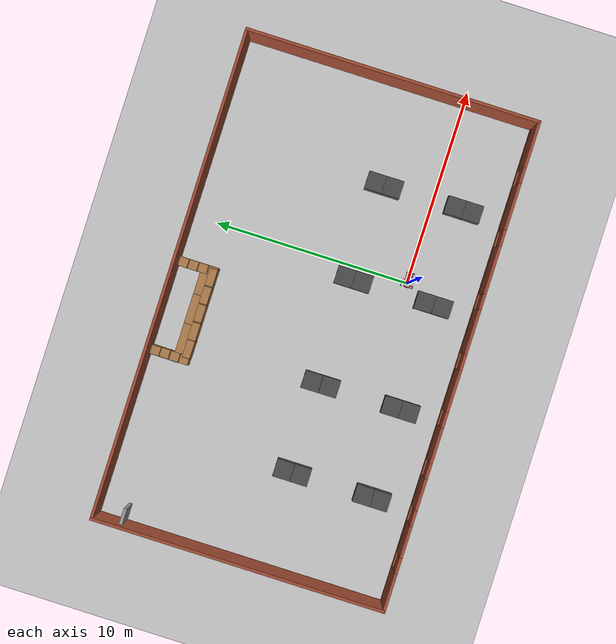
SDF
<sdf version="1.7">
 <world name="default">
  <light name="sun" type="directional">
   <pose>0 0 10 0 -0 0</pose>
   <diffuse>0.8 0.8 0.8 1</diffuse>
   <specular>0.2 0.2 0.2 1</specular>
   <attenuation>
    <range>1000</range>
    <constant>0.9</constant>
    <linear>0.01</linear>
    <quadratic>0.001</quadratic>
   </attenuation>
   <direction>-0.5 0.1 -0.9</direction>
   <spot><inner_angle>0</inner_angle><outer_angle>0</outer_angle><falloff>0</falloff></spot>
  </light>
  <model name="ground_plane">
   <static>1</static>
   <link name="link">
    <collision name="collision">
     <geometry><plane><normal>0 0 1</normal><size>100 100</size></plane></geometry>
     <surface><friction><ode><mu>100</mu><mu2>50</mu2></ode></friction></surface>
    </collision>
    <visual name="visual">
     <cast_shadows>0</cast_shadows>
     <geometry><plane><normal>0 0 1</normal><size>100 100</size></plane></geometry>
     <material>
      <script><uri>file://media/materials/scripts/gazebo.material</uri><name>Gazebo/Grey</name></script>
     </material>
    </visual>
   </link>
  </model>
  <gravity>0 0 -9.8</gravity>
  <magnetic_field>6e-06 2.3e-05 -4.2e-05</magnetic_field>
  <atmosphere type="adiabatic"/>
  <physics type="ode">
   <max_step_size>0.001</max_step_size>
   <real_time_factor>1</real_time_factor>
   <real_time_update_rate>1000</real_time_update_rate>
  </physics>
  <scene><ambient>0.4 0.4 0.4 1</ambient><background>0.7 0.7 0.7 1</background><shadows>1</shadows></scene>
  <audio><device>default</device></audio>
  <spherical_coordinates>
   <surface_model>EARTH_WGS84</surface_model>
   <latitude_deg>0</latitude_deg>
   <longitude_deg>0</longitude_deg>
   <elevation>0</elevation>
   <heading_deg>0</heading_deg>
  </spherical_coordinates>
  <model name="med_walls">
   <pose>-3.1637 3.8217 0 0 -0 0</pose>
   <link name="Door_1">
    <collision name="Door_1_Collision">
     <geometry><box><size>0.9 0.17 2</size></box></geometry>
     <pose>0 0 1 0 -0 0</pose>
    </collision>
    <visual name="Door_1_Visual">
     <pose>0 0 1 0 -0 0</pose>
     <geometry><box><size>0.9 0.17 2</size></box></geometry>
     <material>
      <script><uri>file://media/materials/scripts/gazebo.material</uri><name>Gazebo/Grey</name></script>
     </material>
    </visual>
    <pose>-11.9817 6.03627 0 0 -0 0</pose>
   </link>
   <link name="Wall_10">
    <pose>0 -7.425 0 0 -0 0</pose>
    <visual name="Wall_10_Visual_0">
     <pose>-11.4954 0 1.25 0 -0 0</pose>
     <geometry><box><size>2.00915 0.15 2.5</size></box></geometry>
     <material>
      <script><uri>file://media/materials/scripts/gazebo.material</uri><name>Gazebo/Bricks</name></script>
      <ambient>1 1 1 1</ambient>
     </material>
     <meta><layer>0</layer></meta>
    </visual>
    <collision name="Wall_10_Collision_0">
     <geometry><box><size>2.00915 0.15 2.5</size></box></geometry>
     <pose>-11.4954 0 1.25 0 -0 0</pose>
    </collision>
    <visual name="Wall_10_Visual_1">
     <pose>1.00457 0 0.25 0 -0 0</pose>
     <geometry><box><size>22.9909 0.15 0.5</size></box></geometry>
     <material>
      <script><uri>file://media/materials/scripts/gazebo.material</uri><name>Gazebo/Bricks</name></script>
      <ambient>1 1 1 1</ambient>
     </material>
     <meta><layer>0</layer></meta>
    </visual>
    <collision name="Wall_10_Collision_1">
     <geometry><box><size>22.9909 0.15 0.5</size></box></geometry>
     <pose>1.00457 0 0.25 0 -0 0</pose>
    </collision>
    <visual name="Wall_10_Visual_2">
     <pose>-8.88936 0 1.5 0 -0 0</pose>
     <geometry><box><size>1.60298 0.15 2</size></box></geometry>
     <material>
      <script><uri>file://media/materials/scripts/gazebo.material</uri><name>Gazebo/Bricks</name></script>
      <ambient>1 1 1 1</ambient>
     </material>
     <meta><layer>0</layer></meta>
    </visual>
    <collision name="Wall_10_Collision_2">
     <geometry><box><size>1.60298 0.15 2</size></box></geometry>
     <pose>-8.88936 0 1.5 0 -0 0</pose>
    </collision>
    <visual name="Wall_10_Visual_3">
     <pose>-6.49398 0 1.5 0 -0 0</pose>
     <geometry><box><size>1.58777 0.15 2</size></box></geometry>
     <material>
      <script><uri>file://media/materials/scripts/gazebo.material</uri><name>Gazebo/Bricks</name></script>
      <ambient>1 1 1 1</ambient>
     </material>
     <meta><layer>0</layer></meta>
    </visual>
    <collision name="Wall_10_Collision_3">
     <geometry><box><size>1.58777 0.15 2</size></box></geometry>
     <pose>-6.49398 0 1.5 0 -0 0</pose>
    </collision>
    <visual name="Wall_10_Visual_4">
     <pose>-3.99975 0 1.5 0 -0 0</pose>
     <geometry><box><size>1.8007 0.15 2</size></box></geometry>
     <material>
      <script><uri>file://media/materials/scripts/gazebo.material</uri><name>Gazebo/Bricks</name></script>
      <ambient>1 1 1 1</ambient>
     </material>
     <meta><layer>0</layer></meta>
    </visual>
    <collision name="Wall_10_Collision_4">
     <geometry><box><size>1.8007 0.15 2</size></box></geometry>
     <pose>-3.99975 0 1.5 0 -0 0</pose>
    </collision>
    <visual name="Wall_10_Visual_5">
     <pose>-1.23175 0 1.5 0 -0 0</pose>
     <geometry><box><size>2.13529 0.15 2</size></box></geometry>
     <material>
      <script><uri>file://media/materials/scripts/gazebo.material</uri><name>Gazebo/Bricks</name></script>
      <ambient>1 1 1 1</ambient>
     </material>
     <meta><layer>0</layer></meta>
    </visual>
    <collision name="Wall_10_Collision_5">
     <geometry><box><size>2.13529 0.15 2</size></box></geometry>
     <pose>-1.23175 0 1.5 0 -0 0</pose>
    </collision>
    <visual name="Wall_10_Visual_6">
     <pose>1.77197 0 1.5 0 -0 0</pose>
     <geometry><box><size>2.27217 0.15 2</size></box></geometry>
     <material>
      <script><uri>file://media/materials/scripts/gazebo.material</uri><name>Gazebo/Bricks</name></script>
      <ambient>1 1 1 1</ambient>
     </material>
     <meta><layer>0</layer></meta>
    </visual>
    <collision name="Wall_10_Collision_6">
     <geometry><box><size>2.27217 0.15 2</size></box></geometry>
     <pose>1.77197 0 1.5 0 -0 0</pose>
    </collision>
    <visual name="Wall_10_Visual_7">
     <pose>4.92779 0 1.5 0 -0 0</pose>
     <geometry><box><size>2.43946 0.15 2</size></box></geometry>
     <material>
      <script><uri>file://media/materials/scripts/gazebo.material</uri><name>Gazebo/Bricks</name></script>
      <ambient>1 1 1 1</ambient>
     </material>
     <meta><layer>0</layer></meta>
    </visual>
    <collision name="Wall_10_Collision_7">
     <geometry><box><size>2.43946 0.15 2</size></box></geometry>
     <pose>4.92779 0 1.5 0 -0 0</pose>
    </collision>
    <visual name="Wall_10_Visual_8">
     <pose>8.12923 0 1.5 0 -0 0</pose>
     <geometry><box><size>2.36342 0.15 2</size></box></geometry>
     <material>
      <script><uri>file://media/materials/scripts/gazebo.material</uri><name>Gazebo/Bricks</name></script>
      <ambient>1 1 1 1</ambient>
     </material>
     <meta><layer>0</layer></meta>
    </visual>
    <collision name="Wall_10_Collision_8">
     <geometry><box><size>2.36342 0.15 2</size></box></geometry>
     <pose>8.12923 0 1.5 0 -0 0</pose>
    </collision>
    <visual name="Wall_10_Visual_9">
     <pose>11.3055 0 1.5 0 -0 0</pose>
     <geometry><box><size>2.38906 0.15 2</size></box></geometry>
     <material>
      <script><uri>file://media/materials/scripts/gazebo.material</uri><name>Gazebo/Bricks</name></script>
      <ambient>1 1 1 1</ambient>
     </material>
     <meta><layer>0</layer></meta>
    </visual>
    <collision name="Wall_10_Collision_9">
     <geometry><box><size>2.38906 0.15 2</size></box></geometry>
     <pose>11.3055 0 1.5 0 -0 0</pose>
    </collision>
    <visual name="Wall_10_Visual_10">
     <pose>-10.0909 0 1.9 0 -0 0</pose>
     <geometry><box><size>0.8 0.15 1.2</size></box></geometry>
     <material>
      <script><uri>file://media/materials/scripts/gazebo.material</uri><name>Gazebo/Bricks</name></script>
      <ambient>1 1 1 1</ambient>
     </material>
     <meta><layer>0</layer></meta>
    </visual>
    <collision name="Wall_10_Collision_10">
     <geometry><box><size>0.8 0.15 1.2</size></box></geometry>
     <pose>-10.0909 0 1.9 0 -0 0</pose>
    </collision>
    <visual name="Wall_10_Visual_11">
     <pose>-7.68787 0 1.9 0 -0 0</pose>
     <geometry><box><size>0.8 0.15 1.2</size></box></geometry>
     <material>
      <script><uri>file://media/materials/scripts/gazebo.material</uri><name>Gazebo/Bricks</name></script>
      <ambient>1 1 1 1</ambient>
     </material>
     <meta><layer>0</layer></meta>
    </visual>
    <collision name="Wall_10_Collision_11">
     <geometry><box><size>0.8 0.15 1.2</size></box></geometry>
     <pose>-7.68787 0 1.9 0 -0 0</pose>
    </collision>
    <visual name="Wall_10_Visual_12">
     <pose>-5.3001 0 1.9 0 -0 0</pose>
     <geometry><box><size>0.8 0.15 1.2</size></box></geometry>
     <material>
      <script><uri>file://media/materials/scripts/gazebo.material</uri><name>Gazebo/Bricks</name></script>
      <ambient>1 1 1 1</ambient>
     </material>
     <meta><layer>0</layer></meta>
    </visual>
    <collision name="Wall_10_Collision_12">
     <geometry><box><size>0.8 0.15 1.2</size></box></geometry>
     <pose>-5.3001 0 1.9 0 -0 0</pose>
    </collision>
    <visual name="Wall_10_Visual_13">
     <pose>-2.6994 0 1.9 0 -0 0</pose>
     <geometry><box><size>0.8 0.15 1.2</size></box></geometry>
     <material>
      <script><uri>file://media/materials/scripts/gazebo.material</uri><name>Gazebo/Bricks</name></script>
      <ambient>1 1 1 1</ambient>
     </material>
     <meta><layer>0</layer></meta>
    </visual>
    <collision name="Wall_10_Collision_13">
     <geometry><box><size>0.8 0.15 1.2</size></box></geometry>
     <pose>-2.6994 0 1.9 0 -0 0</pose>
    </collision>
    <visual name="Wall_10_Visual_14">
     <pose>0.235889 0 1.9 0 -0 0</pose>
     <geometry><box><size>0.8 0.15 1.2</size></box></geometry>
     <material>
      <script><uri>file://media/materials/scripts/gazebo.material</uri><name>Gazebo/Bricks</name></script>
      <ambient>1 1 1 1</ambient>
     </material>
     <meta><layer>0</layer></meta>
    </visual>
    <collision name="Wall_10_Collision_14">
     <geometry><box><size>0.8 0.15 1.2</size></box></geometry>
     <pose>0.235889 0 1.9 0 -0 0</pose>
    </collision>
    <visual name="Wall_10_Visual_15">
     <pose>3.30806 0 1.9 0 -0 0</pose>
     <geometry><box><size>0.8 0.15 1.2</size></box></geometry>
     <material>
      <script><uri>file://media/materials/scripts/gazebo.material</uri><name>Gazebo/Bricks</name></script>
      <ambient>1 1 1 1</ambient>
     </material>
     <meta><layer>0</layer></meta>
    </visual>
    <collision name="Wall_10_Collision_15">
     <geometry><box><size>0.8 0.15 1.2</size></box></geometry>
     <pose>3.30806 0 1.9 0 -0 0</pose>
    </collision>
    <visual name="Wall_10_Visual_16">
     <pose>6.54752 0 1.9 0 -0 0</pose>
     <geometry><box><size>0.8 0.15 1.2</size></box></geometry>
     <material>
      <script><uri>file://media/materials/scripts/gazebo.material</uri><name>Gazebo/Bricks</name></script>
      <ambient>1 1 1 1</ambient>
     </material>
     <meta><layer>0</layer></meta>
    </visual>
    <collision name="Wall_10_Collision_16">
     <geometry><box><size>0.8 0.15 1.2</size></box></geometry>
     <pose>6.54752 0 1.9 0 -0 0</pose>
    </collision>
    <visual name="Wall_10_Visual_17">
     <pose>9.71094 0 1.9 0 -0 0</pose>
     <geometry><box><size>0.8 0.15 1.2</size></box></geometry>
     <material>
      <script><uri>file://media/materials/scripts/gazebo.material</uri><name>Gazebo/Bricks</name></script>
      <ambient>1 1 1 1</ambient>
     </material>
     <meta><layer>0</layer></meta>
    </visual>
    <collision name="Wall_10_Collision_17">
     <geometry><box><size>0.8 0.15 1.2</size></box></geometry>
     <pose>9.71094 0 1.9 0 -0 0</pose>
    </collision>
   </link>
   <link name="Wall_17">
    <collision name="Wall_17_Collision">
     <geometry><box><size>15 0.15 2.5</size></box></geometry>
     <pose>0 0 1.25 0 -0 0</pose>
    </collision>
    <visual name="Wall_17_Visual">
     <pose>0 0 1.25 0 -0 0</pose>
     <geometry><box><size>15 0.15 2.5</size></box></geometry>
     <material>
      <script><uri>file://media/materials/scripts/gazebo.material</uri><name>Gazebo/Bricks</name></script>
      <ambient>1 1 1 1</ambient>
     </material>
     <meta><layer>0</layer></meta>
    </visual>
    <pose>12.425 0 0 0 -0 1.5708</pose>
   </link>
   <link name="Wall_19">
    <collision name="Wall_19_Collision">
     <geometry><box><size>15 0.15 2.5</size></box></geometry>
     <pose>0 0 1.25 0 -0 0</pose>
    </collision>
    <visual name="Wall_19_Visual">
     <pose>0 0 1.25 0 -0 0</pose>
     <geometry><box><size>15 0.15 2.5</size></box></geometry>
     <material>
      <script><uri>file://media/materials/scripts/gazebo.material</uri><name>Gazebo/Bricks</name></script>
      <ambient>1 1 1 1</ambient>
     </material>
     <meta><layer>0</layer></meta>
    </visual>
    <pose>-12.425 0 0 0 -0 1.5708</pose>
   </link>
   <link name="Wall_21">
    <collision name="Wall_21_Collision">
     <geometry><box><size>25 0.15 2.5</size></box></geometry>
     <pose>0 0 1.25 0 -0 0</pose>
    </collision>
    <visual name="Wall_21_Visual">
     <pose>0 0 1.25 0 -0 0</pose>
     <geometry><box><size>25 0.15 2.5</size></box></geometry>
     <material>
      <script><uri>file://media/materials/scripts/gazebo.material</uri><name>Gazebo/Bricks</name></script>
      <ambient>1 1 1 1</ambient>
     </material>
     <meta><layer>0</layer></meta>
    </visual>
    <pose>0 7.425 0 0 -0 0</pose>
   </link>
   <static>1</static>
  </model>
  <model name="table">
   <static>1</static>
   <link name="link">
    <collision name="surface">
     <pose>0 0 1 0 -0 0</pose>
     <geometry><box><size>1.5 0.8 0.03</size></box></geometry>
     <surface><friction><ode><mu>0.6</mu><mu2>0.6</mu2></ode></friction></surface>
    </collision>
    <visual name="visual1">
     <pose>0 0 1 0 -0 0</pose>
     <geometry><box><size>1.5 0.8 0.03</size></box></geometry>
     <material>
      <script><uri>file://media/materials/scripts/gazebo.material</uri><name>Gazebo/Wood</name></script>
     </material>
    </visual>
    <collision name="front_left_leg">
     <pose>0.68 0.38 0.5 0 -0 0</pose>
     <geometry><cylinder><radius>0.02</radius><length>1</length></cylinder></geometry>
    </collision>
    <visual name="front_left_leg">
     <pose>0.68 0.38 0.5 0 -0 0</pose>
     <geometry><cylinder><radius>0.02</radius><length>1</length></cylinder></geometry>
     <material>
      <script><uri>file://media/materials/scripts/gazebo.material</uri><name>Gazebo/Grey</name></script>
     </material>
    </visual>
    <collision name="front_right_leg">
     <pose>0.68 -0.38 0.5 0 -0 0</pose>
     <geometry><cylinder><radius>0.02</radius><length>1</length></cylinder></geometry>
    </collision>
    <visual name="front_right_leg">
     <pose>0.68 -0.38 0.5 0 -0 0</pose>
     <geometry><cylinder><radius>0.02</radius><length>1</length></cylinder></geometry>
     <material>
      <script><uri>file://media/materials/scripts/gazebo.material</uri><name>Gazebo/Grey</name></script>
     </material>
    </visual>
    <collision name="back_right_leg">
     <pose>-0.68 -0.38 0.5 0 -0 0</pose>
     <geometry><cylinder><radius>0.02</radius><length>1</length></cylinder></geometry>
    </collision>
    <visual name="back_right_leg">
     <pose>-0.68 -0.38 0.5 0 -0 0</pose>
     <geometry><cylinder><radius>0.02</radius><length>1</length></cylinder></geometry>
     <material>
      <script><uri>file://media/materials/scripts/gazebo.material</uri><name>Gazebo/Grey</name></script>
     </material>
    </visual>
    <collision name="back_left_leg">
     <pose>-0.68 0.38 0.5 0 -0 0</pose>
     <geometry><cylinder><radius>0.02</radius><length>1</length></cylinder></geometry>
    </collision>
    <visual name="back_left_leg">
     <pose>-0.68 0.38 0.5 0 -0 0</pose>
     <geometry><cylinder><radius>0.02</radius><length>1</length></cylinder></geometry>
     <material>
      <script><uri>file://media/materials/scripts/gazebo.material</uri><name>Gazebo/Grey</name></script>
     </material>
    </visual>
   </link>
   <pose>-5.99294 9.5753 0 0 -0 0</pose>
  </model>
  <model name="table_clone">
   <static>1</static>
   <link name="link">
    <collision name="surface">
     <pose>0 0 1 0 -0 0</pose>
     <geometry><box><size>1.5 0.8 0.03</size></box></geometry>
     <surface><friction><ode><mu>0.6</mu><mu2>0.6</mu2></ode></friction></surface>
    </collision>
    <visual name="visual1">
     <pose>0 0 1 0 -0 0</pose>
     <geometry><box><size>1.5 0.8 0.03</size></box></geometry>
     <material>
      <script><uri>file://media/materials/scripts/gazebo.material</uri><name>Gazebo/Wood</name></script>
     </material>
    </visual>
    <collision name="front_left_leg">
     <pose>0.68 0.38 0.5 0 -0 0</pose>
     <geometry><cylinder><radius>0.02</radius><length>1</length></cylinder></geometry>
    </collision>
    <visual name="front_left_leg">
     <pose>0.68 0.38 0.5 0 -0 0</pose>
     <geometry><cylinder><radius>0.02</radius><length>1</length></cylinder></geometry>
     <material>
      <script><uri>file://media/materials/scripts/gazebo.material</uri><name>Gazebo/Grey</name></script>
     </material>
    </visual>
    <collision name="front_right_leg">
     <pose>0.68 -0.38 0.5 0 -0 0</pose>
     <geometry><cylinder><radius>0.02</radius><length>1</length></cylinder></geometry>
    </collision>
    <visual name="front_right_leg">
     <pose>0.68 -0.38 0.5 0 -0 0</pose>
     <geometry><cylinder><radius>0.02</radius><length>1</length></cylinder></geometry>
     <material>
      <script><uri>file://media/materials/scripts/gazebo.material</uri><name>Gazebo/Grey</name></script>
     </material>
    </visual>
    <collision name="back_right_leg">
     <pose>-0.68 -0.38 0.5 0 -0 0</pose>
     <geometry><cylinder><radius>0.02</radius><length>1</length></cylinder></geometry>
    </collision>
    <visual name="back_right_leg">
     <pose>-0.68 -0.38 0.5 0 -0 0</pose>
     <geometry><cylinder><radius>0.02</radius><length>1</length></cylinder></geometry>
     <material>
      <script><uri>file://media/materials/scripts/gazebo.material</uri><name>Gazebo/Grey</name></script>
     </material>
    </visual>
    <collision name="back_left_leg">
     <pose>-0.68 0.38 0.5 0 -0 0</pose>
     <geometry><cylinder><radius>0.02</radius><length>1</length></cylinder></geometry>
    </collision>
    <visual name="back_left_leg">
     <pose>-0.68 0.38 0.5 0 -0 0</pose>
     <geometry><cylinder><radius>0.02</radius><length>1</length></cylinder></geometry>
     <material>
      <script><uri>file://media/materials/scripts/gazebo.material</uri><name>Gazebo/Grey</name></script>
     </material>
    </visual>
   </link>
   <pose>-4.47492 9.5753 0 0 -0 0</pose>
  </model>
  <model name="table_clone_0">
   <static>1</static>
   <link name="link">
    <collision name="surface">
     <pose>0 0 1 0 -0 0</pose>
     <geometry><box><size>1.5 0.8 0.03</size></box></geometry>
     <surface><friction><ode><mu>0.6</mu><mu2>0.6</mu2></ode></friction></surface>
    </collision>
    <visual name="visual1">
     <pose>0 0 1 0 -0 0</pose>
     <geometry><box><size>1.5 0.8 0.03</size></box></geometry>
     <material>
      <script><uri>file://media/materials/scripts/gazebo.material</uri><name>Gazebo/Wood</name></script>
     </material>
    </visual>
    <collision name="front_left_leg">
     <pose>0.68 0.38 0.5 0 -0 0</pose>
     <geometry><cylinder><radius>0.02</radius><length>1</length></cylinder></geometry>
    </collision>
    <visual name="front_left_leg">
     <pose>0.68 0.38 0.5 0 -0 0</pose>
     <geometry><cylinder><radius>0.02</radius><length>1</length></cylinder></geometry>
     <material>
      <script><uri>file://media/materials/scripts/gazebo.material</uri><name>Gazebo/Grey</name></script>
     </material>
    </visual>
    <collision name="front_right_leg">
     <pose>0.68 -0.38 0.5 0 -0 0</pose>
     <geometry><cylinder><radius>0.02</radius><length>1</length></cylinder></geometry>
    </collision>
    <visual name="front_right_leg">
     <pose>0.68 -0.38 0.5 0 -0 0</pose>
     <geometry><cylinder><radius>0.02</radius><length>1</length></cylinder></geometry>
     <material>
      <script><uri>file://media/materials/scripts/gazebo.material</uri><name>Gazebo/Grey</name></script>
     </material>
    </visual>
    <collision name="back_right_leg">
     <pose>-0.68 -0.38 0.5 0 -0 0</pose>
     <geometry><cylinder><radius>0.02</radius><length>1</length></cylinder></geometry>
    </collision>
    <visual name="back_right_leg">
     <pose>-0.68 -0.38 0.5 0 -0 0</pose>
     <geometry><cylinder><radius>0.02</radius><length>1</length></cylinder></geometry>
     <material>
      <script><uri>file://media/materials/scripts/gazebo.material</uri><name>Gazebo/Grey</name></script>
     </material>
    </visual>
    <collision name="back_left_leg">
     <pose>-0.68 0.38 0.5 0 -0 0</pose>
     <geometry><cylinder><radius>0.02</radius><length>1</length></cylinder></geometry>
    </collision>
    <visual name="back_left_leg">
     <pose>-0.68 0.38 0.5 0 -0 0</pose>
     <geometry><cylinder><radius>0.02</radius><length>1</length></cylinder></geometry>
     <material>
      <script><uri>file://media/materials/scripts/gazebo.material</uri><name>Gazebo/Grey</name></script>
     </material>
    </visual>
   </link>
   <pose>-2.95957 9.5753 0 0 -0 0</pose>
  </model>
  <model name="cabinet_clone_0">
   <static>1</static>
   <link name="cabinet_bottom_plate">
    <inertial>
     <pose>0 0 -1 0 -0 0</pose>
     <inertia><ixx>2.05</ixx><ixy>0</ixy><ixz>0</ixz><iyy>2.05</iyy><iyz>0</iyz><izz>2.05</izz></inertia>
     <mass>25</mass>
    </inertial>
    <collision name="cabinet_bottom_plate_geom">
     <pose>0 0 0.01 0 -0 0</pose>
     <geometry><box><size>0.45 0.45 0.02</size></box></geometry>
    </collision>
    <visual name="cabinet_bottom_plate_geom_visual">
     <pose>0 0 0.01 0 -0 0</pose>
     <geometry><box><size>0.45 0.45 0.02</size></box></geometry>
     <material>
      <script><uri>file://media/materials/scripts/gazebo.material</uri><name>Gazebo/Wood</name></script>
     </material>
    </visual>
    <collision name="cabinet_bottom_plate_geom_cabinet_back_plate">
     <pose>0.235 0 0.51 0 -0 0</pose>
     <geometry><box><size>0.02 0.45 1.02</size></box></geometry>
    </collision>
    <visual name="cabinet_bottom_plate_geom_cabinet_back_plate_visual">
     <pose>0.235 0 0.51 0 -0 0</pose>
     <geometry><box><size>0.02 0.45 1.02</size></box></geometry>
     <material>
      <script><uri>file://media/materials/scripts/gazebo.material</uri><name>Gazebo/Wood</name></script>
     </material>
    </visual>
    <collision name="cabinet_bottom_plate_geom_cabinet_left_plate">
     <pose>0 0.235 0.51 0 -0 0</pose>
     <geometry><box><size>0.45 0.02 1.02</size></box></geometry>
    </collision>
    <visual name="cabinet_bottom_plate_geom_cabinet_left_plate_visual">
     <pose>0 0.235 0.51 0 -0 0</pose>
     <geometry><box><size>0.45 0.02 1.02</size></box></geometry>
     <material>
      <script><uri>file://media/materials/scripts/gazebo.material</uri><name>Gazebo/Wood</name></script>
     </material>
    </visual>
    <collision name="cabinet_bottom_plate_geom_cabinet_middle_plate">
     <pose>0 0 0.51 0 -0 0</pose>
     <geometry><box><size>0.45 0.45 0.02</size></box></geometry>
    </collision>
    <visual name="cabinet_bottom_plate_geom_cabinet_middle_plate_visual">
     <pose>0 0 0.51 0 -0 0</pose>
     <geometry><box><size>0.45 0.45 0.02</size></box></geometry>
     <material>
      <script><uri>file://media/materials/scripts/gazebo.material</uri><name>Gazebo/Wood</name></script>
     </material>
    </visual>
    <collision name="cabinet_bottom_plate_geom_cabinet_right_plate">
     <pose>0 -0.235 0.51 0 -0 0</pose>
     <geometry><box><size>0.45 0.02 1.02</size></box></geometry>
    </collision>
    <visual name="cabinet_bottom_plate_geom_cabinet_right_plate_visual">
     <pose>0 -0.235 0.51 0 -0 0</pose>
     <geometry><box><size>0.45 0.02 1.02</size></box></geometry>
     <material>
      <script><uri>file://media/materials/scripts/gazebo.material</uri><name>Gazebo/Wood</name></script>
     </material>
    </visual>
    <collision name="cabinet_bottom_plate_geom_cabinet_top_plate">
     <pose>0 0 1.01 0 -0 0</pose>
     <geometry><box><size>0.45 0.45 0.02</size></box></geometry>
    </collision>
    <visual name="cabinet_bottom_plate_geom_cabinet_top_plate_visual">
     <pose>0 0 1.01 0 -0 0</pose>
     <geometry><box><size>0.45 0.45 0.02</size></box></geometry>
     <material>
      <script><uri>file://media/materials/scripts/gazebo.material</uri><name>Gazebo/Wood</name></script>
     </material>
    </visual>
   </link>
   <pose>-6.97745 9.41498 0 0 -0 0</pose>
  </model>
  <model name="bookshelf">
   <static>1</static>
   <link name="link">
    <inertial><mass>1</mass></inertial>
    <collision name="back">
     <pose>0 0.005 0.6 0 -0 0</pose>
     <geometry><box><size>0.9 0.01 1.2</size></box></geometry>
    </collision>
    <visual name="visual1">
     <pose>0 0.005 0.6 0 -0 0</pose>
     <geometry><box><size>0.9 0.01 1.2</size></box></geometry>
     <material>
      <script><uri>file://media/materials/scripts/gazebo.material</uri><name>Gazebo/Wood</name></script>
     </material>
    </visual>
    <collision name="left_side">
     <pose>0.45 -0.195 0.6 0 -0 0</pose>
     <geometry><box><size>0.02 0.4 1.2</size></box></geometry>
    </collision>
    <visual name="visual2">
     <pose>0.45 -0.195 0.6 0 -0 0</pose>
     <geometry><box><size>0.02 0.4 1.2</size></box></geometry>
     <material>
      <script><uri>file://media/materials/scripts/gazebo.material</uri><name>Gazebo/Wood</name></script>
     </material>
    </visual>
    <collision name="right_side">
     <pose>-0.45 -0.195 0.6 0 -0 0</pose>
     <geometry><box><size>0.02 0.4 1.2</size></box></geometry>
    </collision>
    <visual name="visual3">
     <pose>-0.45 -0.195 0.6 0 -0 0</pose>
     <geometry><box><size>0.02 0.4 1.2</size></box></geometry>
     <material>
      <script><uri>file://media/materials/scripts/gazebo.material</uri><name>Gazebo/Wood</name></script>
     </material>
    </visual>
    <collision name="bottom">
     <pose>0 -0.195 0.03 0 -0 0</pose>
     <geometry><box><size>0.88 0.4 0.06</size></box></geometry>
    </collision>
    <visual name="visual4">
     <pose>0 -0.195 0.03 0 -0 0</pose>
     <geometry><box><size>0.88 0.4 0.06</size></box></geometry>
     <material>
      <script><uri>file://media/materials/scripts/gazebo.material</uri><name>Gazebo/Wood</name></script>
     </material>
    </visual>
    <collision name="top">
     <pose>0 -0.195 1.19 0 -0 0</pose>
     <geometry><box><size>0.88 0.4 0.02</size></box></geometry>
    </collision>
    <visual name="visual5">
     <pose>0 -0.195 1.19 0 -0 0</pose>
     <geometry><box><size>0.88 0.4 0.02</size></box></geometry>
     <material>
      <script><uri>file://media/materials/scripts/gazebo.material</uri><name>Gazebo/Wood</name></script>
     </material>
    </visual>
    <collision name="low_shelf">
     <pose>0 -0.195 0.43 0 -0 0</pose>
     <geometry><box><size>0.88 0.4 0.02</size></box></geometry>
    </collision>
    <visual name="visual6">
     <pose>0 -0.195 0.43 0 -0 0</pose>
     <geometry><box><size>0.88 0.4 0.02</size></box></geometry>
     <material>
      <script><uri>file://media/materials/scripts/gazebo.material</uri><name>Gazebo/Wood</name></script>
     </material>
    </visual>
    <collision name="high_shelf">
     <pose>0 -0.195 0.8 0 -0 0</pose>
     <geometry><box><size>0.88 0.4 0.02</size></box></geometry>
    </collision>
    <visual name="visual7">
     <pose>0 -0.195 0.8 0 -0 0</pose>
     <geometry><box><size>0.88 0.4 0.02</size></box></geometry>
     <material>
      <script><uri>file://media/materials/scripts/gazebo.material</uri><name>Gazebo/Wood</name></script>
     </material>
    </visual>
   </link>
   <pose>-2.70056 9.16191 0 0 -0 3.13728</pose>
  </model>
  <model name="bookshelf_clone">
   <static>1</static>
   <link name="link">
    <inertial><mass>1</mass></inertial>
    <collision name="back">
     <pose>0 0.005 0.6 0 -0 0</pose>
     <geometry><box><size>0.9 0.01 1.2</size></box></geometry>
    </collision>
    <visual name="visual1">
     <pose>0 0.005 0.6 0 -0 0</pose>
     <geometry><box><size>0.9 0.01 1.2</size></box></geometry>
     <material>
      <script><uri>file://media/materials/scripts/gazebo.material</uri><name>Gazebo/Wood</name></script>
     </material>
    </visual>
    <collision name="left_side">
     <pose>0.45 -0.195 0.6 0 -0 0</pose>
     <geometry><box><size>0.02 0.4 1.2</size></box></geometry>
    </collision>
    <visual name="visual2">
     <pose>0.45 -0.195 0.6 0 -0 0</pose>
     <geometry><box><size>0.02 0.4 1.2</size></box></geometry>
     <material>
      <script><uri>file://media/materials/scripts/gazebo.material</uri><name>Gazebo/Wood</name></script>
     </material>
    </visual>
    <collision name="right_side">
     <pose>-0.45 -0.195 0.6 0 -0 0</pose>
     <geometry><box><size>0.02 0.4 1.2</size></box></geometry>
    </collision>
    <visual name="visual3">
     <pose>-0.45 -0.195 0.6 0 -0 0</pose>
     <geometry><box><size>0.02 0.4 1.2</size></box></geometry>
     <material>
      <script><uri>file://media/materials/scripts/gazebo.material</uri><name>Gazebo/Wood</name></script>
     </material>
    </visual>
    <collision name="bottom">
     <pose>0 -0.195 0.03 0 -0 0</pose>
     <geometry><box><size>0.88 0.4 0.06</size></box></geometry>
    </collision>
    <visual name="visual4">
     <pose>0 -0.195 0.03 0 -0 0</pose>
     <geometry><box><size>0.88 0.4 0.06</size></box></geometry>
     <material>
      <script><uri>file://media/materials/scripts/gazebo.material</uri><name>Gazebo/Wood</name></script>
     </material>
    </visual>
    <collision name="top">
     <pose>0 -0.195 1.19 0 -0 0</pose>
     <geometry><box><size>0.88 0.4 0.02</size></box></geometry>
    </collision>
    <visual name="visual5">
     <pose>0 -0.195 1.19 0 -0 0</pose>
     <geometry><box><size>0.88 0.4 0.02</size></box></geometry>
     <material>
      <script><uri>file://media/materials/scripts/gazebo.material</uri><name>Gazebo/Wood</name></script>
     </material>
    </visual>
    <collision name="low_shelf">
     <pose>0 -0.195 0.43 0 -0 0</pose>
     <geometry><box><size>0.88 0.4 0.02</size></box></geometry>
    </collision>
    <visual name="visual6">
     <pose>0 -0.195 0.43 0 -0 0</pose>
     <geometry><box><size>0.88 0.4 0.02</size></box></geometry>
     <material>
      <script><uri>file://media/materials/scripts/gazebo.material</uri><name>Gazebo/Wood</name></script>
     </material>
    </visual>
    <collision name="high_shelf">
     <pose>0 -0.195 0.8 0 -0 0</pose>
     <geometry><box><size>0.88 0.4 0.02</size></box></geometry>
    </collision>
    <visual name="visual7">
     <pose>0 -0.195 0.8 0 -0 0</pose>
     <geometry><box><size>0.88 0.4 0.02</size></box></geometry>
     <material>
      <script><uri>file://media/materials/scripts/gazebo.material</uri><name>Gazebo/Wood</name></script>
     </material>
    </visual>
   </link>
   <pose>-3.62714 9.16191 0 0 -0 3.13728</pose>
  </model>
  <model name="bookshelf_clone_0">
   <static>1</static>
   <link name="link">
    <inertial><mass>1</mass></inertial>
    <collision name="back">
     <pose>0 0.005 0.6 0 -0 0</pose>
     <geometry><box><size>0.9 0.01 1.2</size></box></geometry>
    </collision>
    <visual name="visual1">
     <pose>0 0.005 0.6 0 -0 0</pose>
     <geometry><box><size>0.9 0.01 1.2</size></box></geometry>
     <material>
      <script><uri>file://media/materials/scripts/gazebo.material</uri><name>Gazebo/Wood</name></script>
     </material>
    </visual>
    <collision name="left_side">
     <pose>0.45 -0.195 0.6 0 -0 0</pose>
     <geometry><box><size>0.02 0.4 1.2</size></box></geometry>
    </collision>
    <visual name="visual2">
     <pose>0.45 -0.195 0.6 0 -0 0</pose>
     <geometry><box><size>0.02 0.4 1.2</size></box></geometry>
     <material>
      <script><uri>file://media/materials/scripts/gazebo.material</uri><name>Gazebo/Wood</name></script>
     </material>
    </visual>
    <collision name="right_side">
     <pose>-0.45 -0.195 0.6 0 -0 0</pose>
     <geometry><box><size>0.02 0.4 1.2</size></box></geometry>
    </collision>
    <visual name="visual3">
     <pose>-0.45 -0.195 0.6 0 -0 0</pose>
     <geometry><box><size>0.02 0.4 1.2</size></box></geometry>
     <material>
      <script><uri>file://media/materials/scripts/gazebo.material</uri><name>Gazebo/Wood</name></script>
     </material>
    </visual>
    <collision name="bottom">
     <pose>0 -0.195 0.03 0 -0 0</pose>
     <geometry><box><size>0.88 0.4 0.06</size></box></geometry>
    </collision>
    <visual name="visual4">
     <pose>0 -0.195 0.03 0 -0 0</pose>
     <geometry><box><size>0.88 0.4 0.06</size></box></geometry>
     <material>
      <script><uri>file://media/materials/scripts/gazebo.material</uri><name>Gazebo/Wood</name></script>
     </material>
    </visual>
    <collision name="top">
     <pose>0 -0.195 1.19 0 -0 0</pose>
     <geometry><box><size>0.88 0.4 0.02</size></box></geometry>
    </collision>
    <visual name="visual5">
     <pose>0 -0.195 1.19 0 -0 0</pose>
     <geometry><box><size>0.88 0.4 0.02</size></box></geometry>
     <material>
      <script><uri>file://media/materials/scripts/gazebo.material</uri><name>Gazebo/Wood</name></script>
     </material>
    </visual>
    <collision name="low_shelf">
     <pose>0 -0.195 0.43 0 -0 0</pose>
     <geometry><box><size>0.88 0.4 0.02</size></box></geometry>
    </collision>
    <visual name="visual6">
     <pose>0 -0.195 0.43 0 -0 0</pose>
     <geometry><box><size>0.88 0.4 0.02</size></box></geometry>
     <material>
      <script><uri>file://media/materials/scripts/gazebo.material</uri><name>Gazebo/Wood</name></script>
     </material>
    </visual>
    <collision name="high_shelf">
     <pose>0 -0.195 0.8 0 -0 0</pose>
     <geometry><box><size>0.88 0.4 0.02</size></box></geometry>
    </collision>
    <visual name="visual7">
     <pose>0 -0.195 0.8 0 -0 0</pose>
     <geometry><box><size>0.88 0.4 0.02</size></box></geometry>
     <material>
      <script><uri>file://media/materials/scripts/gazebo.material</uri><name>Gazebo/Wood</name></script>
     </material>
    </visual>
   </link>
   <pose>-4.55765 9.16191 0 0 -0 3.13728</pose>
  </model>
  <model name="bookshelf_clone_1">
   <static>1</static>
   <link name="link">
    <inertial><mass>1</mass></inertial>
    <collision name="back">
     <pose>0 0.005 0.6 0 -0 0</pose>
     <geometry><box><size>0.9 0.01 1.2</size></box></geometry>
    </collision>
    <visual name="visual1">
     <pose>0 0.005 0.6 0 -0 0</pose>
     <geometry><box><size>0.9 0.01 1.2</size></box></geometry>
     <material>
      <script><uri>file://media/materials/scripts/gazebo.material</uri><name>Gazebo/Wood</name></script>
     </material>
    </visual>
    <collision name="left_side">
     <pose>0.45 -0.195 0.6 0 -0 0</pose>
     <geometry><box><size>0.02 0.4 1.2</size></box></geometry>
    </collision>
    <visual name="visual2">
     <pose>0.45 -0.195 0.6 0 -0 0</pose>
     <geometry><box><size>0.02 0.4 1.2</size></box></geometry>
     <material>
      <script><uri>file://media/materials/scripts/gazebo.material</uri><name>Gazebo/Wood</name></script>
     </material>
    </visual>
    <collision name="right_side">
     <pose>-0.45 -0.195 0.6 0 -0 0</pose>
     <geometry><box><size>0.02 0.4 1.2</size></box></geometry>
    </collision>
    <visual name="visual3">
     <pose>-0.45 -0.195 0.6 0 -0 0</pose>
     <geometry><box><size>0.02 0.4 1.2</size></box></geometry>
     <material>
      <script><uri>file://media/materials/scripts/gazebo.material</uri><name>Gazebo/Wood</name></script>
     </material>
    </visual>
    <collision name="bottom">
     <pose>0 -0.195 0.03 0 -0 0</pose>
     <geometry><box><size>0.88 0.4 0.06</size></box></geometry>
    </collision>
    <visual name="visual4">
     <pose>0 -0.195 0.03 0 -0 0</pose>
     <geometry><box><size>0.88 0.4 0.06</size></box></geometry>
     <material>
      <script><uri>file://media/materials/scripts/gazebo.material</uri><name>Gazebo/Wood</name></script>
     </material>
    </visual>
    <collision name="top">
     <pose>0 -0.195 1.19 0 -0 0</pose>
     <geometry><box><size>0.88 0.4 0.02</size></box></geometry>
    </collision>
    <visual name="visual5">
     <pose>0 -0.195 1.19 0 -0 0</pose>
     <geometry><box><size>0.88 0.4 0.02</size></box></geometry>
     <material>
      <script><uri>file://media/materials/scripts/gazebo.material</uri><name>Gazebo/Wood</name></script>
     </material>
    </visual>
    <collision name="low_shelf">
     <pose>0 -0.195 0.43 0 -0 0</pose>
     <geometry><box><size>0.88 0.4 0.02</size></box></geometry>
    </collision>
    <visual name="visual6">
     <pose>0 -0.195 0.43 0 -0 0</pose>
     <geometry><box><size>0.88 0.4 0.02</size></box></geometry>
     <material>
      <script><uri>file://media/materials/scripts/gazebo.material</uri><name>Gazebo/Wood</name></script>
     </material>
    </visual>
    <collision name="high_shelf">
     <pose>0 -0.195 0.8 0 -0 0</pose>
     <geometry><box><size>0.88 0.4 0.02</size></box></geometry>
    </collision>
    <visual name="visual7">
     <pose>0 -0.195 0.8 0 -0 0</pose>
     <geometry><box><size>0.88 0.4 0.02</size></box></geometry>
     <material>
      <script><uri>file://media/materials/scripts/gazebo.material</uri><name>Gazebo/Wood</name></script>
     </material>
    </visual>
   </link>
   <pose>-5.49467 9.16191 0 0 -0 3.13728</pose>
  </model>
  <model name="bookshelf_clone_2">
   <static>1</static>
   <link name="link">
    <inertial><mass>1</mass></inertial>
    <collision name="back">
     <pose>0 0.005 0.6 0 -0 0</pose>
     <geometry><box><size>0.9 0.01 1.2</size></box></geometry>
    </collision>
    <visual name="visual1">
     <pose>0 0.005 0.6 0 -0 0</pose>
     <geometry><box><size>0.9 0.01 1.2</size></box></geometry>
     <material>
      <script><uri>file://media/materials/scripts/gazebo.material</uri><name>Gazebo/Wood</name></script>
     </material>
    </visual>
    <collision name="left_side">
     <pose>0.45 -0.195 0.6 0 -0 0</pose>
     <geometry><box><size>0.02 0.4 1.2</size></box></geometry>
    </collision>
    <visual name="visual2">
     <pose>0.45 -0.195 0.6 0 -0 0</pose>
     <geometry><box><size>0.02 0.4 1.2</size></box></geometry>
     <material>
      <script><uri>file://media/materials/scripts/gazebo.material</uri><name>Gazebo/Wood</name></script>
     </material>
    </visual>
    <collision name="right_side">
     <pose>-0.45 -0.195 0.6 0 -0 0</pose>
     <geometry><box><size>0.02 0.4 1.2</size></box></geometry>
    </collision>
    <visual name="visual3">
     <pose>-0.45 -0.195 0.6 0 -0 0</pose>
     <geometry><box><size>0.02 0.4 1.2</size></box></geometry>
     <material>
      <script><uri>file://media/materials/scripts/gazebo.material</uri><name>Gazebo/Wood</name></script>
     </material>
    </visual>
    <collision name="bottom">
     <pose>0 -0.195 0.03 0 -0 0</pose>
     <geometry><box><size>0.88 0.4 0.06</size></box></geometry>
    </collision>
    <visual name="visual4">
     <pose>0 -0.195 0.03 0 -0 0</pose>
     <geometry><box><size>0.88 0.4 0.06</size></box></geometry>
     <material>
      <script><uri>file://media/materials/scripts/gazebo.material</uri><name>Gazebo/Wood</name></script>
     </material>
    </visual>
    <collision name="top">
     <pose>0 -0.195 1.19 0 -0 0</pose>
     <geometry><box><size>0.88 0.4 0.02</size></box></geometry>
    </collision>
    <visual name="visual5">
     <pose>0 -0.195 1.19 0 -0 0</pose>
     <geometry><box><size>0.88 0.4 0.02</size></box></geometry>
     <material>
      <script><uri>file://media/materials/scripts/gazebo.material</uri><name>Gazebo/Wood</name></script>
     </material>
    </visual>
    <collision name="low_shelf">
     <pose>0 -0.195 0.43 0 -0 0</pose>
     <geometry><box><size>0.88 0.4 0.02</size></box></geometry>
    </collision>
    <visual name="visual6">
     <pose>0 -0.195 0.43 0 -0 0</pose>
     <geometry><box><size>0.88 0.4 0.02</size></box></geometry>
     <material>
      <script><uri>file://media/materials/scripts/gazebo.material</uri><name>Gazebo/Wood</name></script>
     </material>
    </visual>
    <collision name="high_shelf">
     <pose>0 -0.195 0.8 0 -0 0</pose>
     <geometry><box><size>0.88 0.4 0.02</size></box></geometry>
    </collision>
    <visual name="visual7">
     <pose>0 -0.195 0.8 0 -0 0</pose>
     <geometry><box><size>0.88 0.4 0.02</size></box></geometry>
     <material>
      <script><uri>file://media/materials/scripts/gazebo.material</uri><name>Gazebo/Wood</name></script>
     </material>
    </visual>
   </link>
   <pose>-6.40578 9.16191 0 0 -0 3.13728</pose>
  </model>
  <model name="cabinet_clone_0_clone">
   <static>1</static>
   <link name="cabinet_bottom_plate">
    <inertial>
     <pose>0 0 -1 0 -0 0</pose>
     <inertia><ixx>2.05</ixx><ixy>0</ixy><ixz>0</ixz><iyy>2.05</iyy><iyz>0</iyz><izz>2.05</izz></inertia>
     <mass>25</mass>
    </inertial>
    <collision name="cabinet_bottom_plate_geom">
     <pose>0 0 0.01 0 -0 0</pose>
     <geometry><box><size>0.45 0.45 0.02</size></box></geometry>
    </collision>
    <visual name="cabinet_bottom_plate_geom_visual">
     <pose>0 0 0.01 0 -0 0</pose>
     <geometry><box><size>0.45 0.45 0.02</size></box></geometry>
     <material>
      <script><uri>file://media/materials/scripts/gazebo.material</uri><name>Gazebo/Wood</name></script>
     </material>
    </visual>
    <collision name="cabinet_bottom_plate_geom_cabinet_back_plate">
     <pose>0.235 0 0.51 0 -0 0</pose>
     <geometry><box><size>0.02 0.45 1.02</size></box></geometry>
    </collision>
    <visual name="cabinet_bottom_plate_geom_cabinet_back_plate_visual">
     <pose>0.235 0 0.51 0 -0 0</pose>
     <geometry><box><size>0.02 0.45 1.02</size></box></geometry>
     <material>
      <script><uri>file://media/materials/scripts/gazebo.material</uri><name>Gazebo/Wood</name></script>
     </material>
    </visual>
    <collision name="cabinet_bottom_plate_geom_cabinet_left_plate">
     <pose>0 0.235 0.51 0 -0 0</pose>
     <geometry><box><size>0.45 0.02 1.02</size></box></geometry>
    </collision>
    <visual name="cabinet_bottom_plate_geom_cabinet_left_plate_visual">
     <pose>0 0.235 0.51 0 -0 0</pose>
     <geometry><box><size>0.45 0.02 1.02</size></box></geometry>
     <material>
      <script><uri>file://media/materials/scripts/gazebo.material</uri><name>Gazebo/Wood</name></script>
     </material>
    </visual>
    <collision name="cabinet_bottom_plate_geom_cabinet_middle_plate">
     <pose>0 0 0.51 0 -0 0</pose>
     <geometry><box><size>0.45 0.45 0.02</size></box></geometry>
    </collision>
    <visual name="cabinet_bottom_plate_geom_cabinet_middle_plate_visual">
     <pose>0 0 0.51 0 -0 0</pose>
     <geometry><box><size>0.45 0.45 0.02</size></box></geometry>
     <material>
      <script><uri>file://media/materials/scripts/gazebo.material</uri><name>Gazebo/Wood</name></script>
     </material>
    </visual>
    <collision name="cabinet_bottom_plate_geom_cabinet_right_plate">
     <pose>0 -0.235 0.51 0 -0 0</pose>
     <geometry><box><size>0.45 0.02 1.02</size></box></geometry>
    </collision>
    <visual name="cabinet_bottom_plate_geom_cabinet_right_plate_visual">
     <pose>0 -0.235 0.51 0 -0 0</pose>
     <geometry><box><size>0.45 0.02 1.02</size></box></geometry>
     <material>
      <script><uri>file://media/materials/scripts/gazebo.material</uri><name>Gazebo/Wood</name></script>
     </material>
    </visual>
    <collision name="cabinet_bottom_plate_geom_cabinet_top_plate">
     <pose>0 0 1.01 0 -0 0</pose>
     <geometry><box><size>0.45 0.45 0.02</size></box></geometry>
    </collision>
    <visual name="cabinet_bottom_plate_geom_cabinet_top_plate_visual">
     <pose>0 0 1.01 0 -0 0</pose>
     <geometry><box><size>0.45 0.45 0.02</size></box></geometry>
     <material>
      <script><uri>file://media/materials/scripts/gazebo.material</uri><name>Gazebo/Wood</name></script>
     </material>
    </visual>
   </link>
   <pose>-6.97028 9.91562 0 0 -0 3.13538</pose>
  </model>
  <model name="cabinet_clone_0_clone_0">
   <static>1</static>
   <link name="cabinet_bottom_plate">
    <inertial>
     <pose>0 0 -1 0 -0 0</pose>
     <inertia><ixx>2.05</ixx><ixy>0</ixy><ixz>0</ixz><iyy>2.05</iyy><iyz>0</iyz><izz>2.05</izz></inertia>
     <mass>25</mass>
    </inertial>
    <collision name="cabinet_bottom_plate_geom">
     <pose>0 0 0.01 0 -0 0</pose>
     <geometry><box><size>0.45 0.45 0.02</size></box></geometry>
    </collision>
    <visual name="cabinet_bottom_plate_geom_visual">
     <pose>0 0 0.01 0 -0 0</pose>
     <geometry><box><size>0.45 0.45 0.02</size></box></geometry>
     <material>
      <script><uri>file://media/materials/scripts/gazebo.material</uri><name>Gazebo/Wood</name></script>
     </material>
    </visual>
    <collision name="cabinet_bottom_plate_geom_cabinet_back_plate">
     <pose>0.235 0 0.51 0 -0 0</pose>
     <geometry><box><size>0.02 0.45 1.02</size></box></geometry>
    </collision>
    <visual name="cabinet_bottom_plate_geom_cabinet_back_plate_visual">
     <pose>0.235 0 0.51 0 -0 0</pose>
     <geometry><box><size>0.02 0.45 1.02</size></box></geometry>
     <material>
      <script><uri>file://media/materials/scripts/gazebo.material</uri><name>Gazebo/Wood</name></script>
     </material>
    </visual>
    <collision name="cabinet_bottom_plate_geom_cabinet_left_plate">
     <pose>0 0.235 0.51 0 -0 0</pose>
     <geometry><box><size>0.45 0.02 1.02</size></box></geometry>
    </collision>
    <visual name="cabinet_bottom_plate_geom_cabinet_left_plate_visual">
     <pose>0 0.235 0.51 0 -0 0</pose>
     <geometry><box><size>0.45 0.02 1.02</size></box></geometry>
     <material>
      <script><uri>file://media/materials/scripts/gazebo.material</uri><name>Gazebo/Wood</name></script>
     </material>
    </visual>
    <collision name="cabinet_bottom_plate_geom_cabinet_middle_plate">
     <pose>0 0 0.51 0 -0 0</pose>
     <geometry><box><size>0.45 0.45 0.02</size></box></geometry>
    </collision>
    <visual name="cabinet_bottom_plate_geom_cabinet_middle_plate_visual">
     <pose>0 0 0.51 0 -0 0</pose>
     <geometry><box><size>0.45 0.45 0.02</size></box></geometry>
     <material>
      <script><uri>file://media/materials/scripts/gazebo.material</uri><name>Gazebo/Wood</name></script>
     </material>
    </visual>
    <collision name="cabinet_bottom_plate_geom_cabinet_right_plate">
     <pose>0 -0.235 0.51 0 -0 0</pose>
     <geometry><box><size>0.45 0.02 1.02</size></box></geometry>
    </collision>
    <visual name="cabinet_bottom_plate_geom_cabinet_right_plate_visual">
     <pose>0 -0.235 0.51 0 -0 0</pose>
     <geometry><box><size>0.45 0.02 1.02</size></box></geometry>
     <material>
      <script><uri>file://media/materials/scripts/gazebo.material</uri><name>Gazebo/Wood</name></script>
     </material>
    </visual>
    <collision name="cabinet_bottom_plate_geom_cabinet_top_plate">
     <pose>0 0 1.01 0 -0 0</pose>
     <geometry><box><size>0.45 0.45 0.02</size></box></geometry>
    </collision>
    <visual name="cabinet_bottom_plate_geom_cabinet_top_plate_visual">
     <pose>0 0 1.01 0 -0 0</pose>
     <geometry><box><size>0.45 0.45 0.02</size></box></geometry>
     <material>
      <script><uri>file://media/materials/scripts/gazebo.material</uri><name>Gazebo/Wood</name></script>
     </material>
    </visual>
   </link>
   <pose>-6.96165 10.418 0 0 -0 3.13538</pose>
  </model>
  <model name="cabinet_clone_0_clone_1">
   <static>1</static>
   <link name="cabinet_bottom_plate">
    <inertial>
     <pose>0 0 -1 0 -0 0</pose>
     <inertia><ixx>2.05</ixx><ixy>0</ixy><ixz>0</ixz><iyy>2.05</iyy><iyz>0</iyz><izz>2.05</izz></inertia>
     <mass>25</mass>
    </inertial>
    <collision name="cabinet_bottom_plate_geom">
     <pose>0 0 0.01 0 -0 0</pose>
     <geometry><box><size>0.45 0.45 0.02</size></box></geometry>
    </collision>
    <visual name="cabinet_bottom_plate_geom_visual">
     <pose>0 0 0.01 0 -0 0</pose>
     <geometry><box><size>0.45 0.45 0.02</size></box></geometry>
     <material>
      <script><uri>file://media/materials/scripts/gazebo.material</uri><name>Gazebo/Wood</name></script>
     </material>
    </visual>
    <collision name="cabinet_bottom_plate_geom_cabinet_back_plate">
     <pose>0.235 0 0.51 0 -0 0</pose>
     <geometry><box><size>0.02 0.45 1.02</size></box></geometry>
    </collision>
    <visual name="cabinet_bottom_plate_geom_cabinet_back_plate_visual">
     <pose>0.235 0 0.51 0 -0 0</pose>
     <geometry><box><size>0.02 0.45 1.02</size></box></geometry>
     <material>
      <script><uri>file://media/materials/scripts/gazebo.material</uri><name>Gazebo/Wood</name></script>
     </material>
    </visual>
    <collision name="cabinet_bottom_plate_geom_cabinet_left_plate">
     <pose>0 0.235 0.51 0 -0 0</pose>
     <geometry><box><size>0.45 0.02 1.02</size></box></geometry>
    </collision>
    <visual name="cabinet_bottom_plate_geom_cabinet_left_plate_visual">
     <pose>0 0.235 0.51 0 -0 0</pose>
     <geometry><box><size>0.45 0.02 1.02</size></box></geometry>
     <material>
      <script><uri>file://media/materials/scripts/gazebo.material</uri><name>Gazebo/Wood</name></script>
     </material>
    </visual>
    <collision name="cabinet_bottom_plate_geom_cabinet_middle_plate">
     <pose>0 0 0.51 0 -0 0</pose>
     <geometry><box><size>0.45 0.45 0.02</size></box></geometry>
    </collision>
    <visual name="cabinet_bottom_plate_geom_cabinet_middle_plate_visual">
     <pose>0 0 0.51 0 -0 0</pose>
     <geometry><box><size>0.45 0.45 0.02</size></box></geometry>
     <material>
      <script><uri>file://media/materials/scripts/gazebo.material</uri><name>Gazebo/Wood</name></script>
     </material>
    </visual>
    <collision name="cabinet_bottom_plate_geom_cabinet_right_plate">
     <pose>0 -0.235 0.51 0 -0 0</pose>
     <geometry><box><size>0.45 0.02 1.02</size></box></geometry>
    </collision>
    <visual name="cabinet_bottom_plate_geom_cabinet_right_plate_visual">
     <pose>0 -0.235 0.51 0 -0 0</pose>
     <geometry><box><size>0.45 0.02 1.02</size></box></geometry>
     <material>
      <script><uri>file://media/materials/scripts/gazebo.material</uri><name>Gazebo/Wood</name></script>
     </material>
    </visual>
    <collision name="cabinet_bottom_plate_geom_cabinet_top_plate">
     <pose>0 0 1.01 0 -0 0</pose>
     <geometry><box><size>0.45 0.45 0.02</size></box></geometry>
    </collision>
    <visual name="cabinet_bottom_plate_geom_cabinet_top_plate_visual">
     <pose>0 0 1.01 0 -0 0</pose>
     <geometry><box><size>0.45 0.45 0.02</size></box></geometry>
     <material>
      <script><uri>file://media/materials/scripts/gazebo.material</uri><name>Gazebo/Wood</name></script>
     </material>
    </visual>
   </link>
   <pose>-6.95978 10.9123 0 0 -0 3.13538</pose>
  </model>
  <model name="cabinet_clone_0_clone_2">
   <static>1</static>
   <link name="cabinet_bottom_plate">
    <inertial>
     <pose>0 0 -1 0 -0 0</pose>
     <inertia><ixx>2.05</ixx><ixy>0</ixy><ixz>0</ixz><iyy>2.05</iyy><iyz>0</iyz><izz>2.05</izz></inertia>
     <mass>25</mass>
    </inertial>
    <collision name="cabinet_bottom_plate_geom">
     <pose>0 0 0.01 0 -0 0</pose>
     <geometry><box><size>0.45 0.45 0.02</size></box></geometry>
    </collision>
    <visual name="cabinet_bottom_plate_geom_visual">
     <pose>0 0 0.01 0 -0 0</pose>
     <geometry><box><size>0.45 0.45 0.02</size></box></geometry>
     <material>
      <script><uri>file://media/materials/scripts/gazebo.material</uri><name>Gazebo/Wood</name></script>
     </material>
    </visual>
    <collision name="cabinet_bottom_plate_geom_cabinet_back_plate">
     <pose>0.235 0 0.51 0 -0 0</pose>
     <geometry><box><size>0.02 0.45 1.02</size></box></geometry>
    </collision>
    <visual name="cabinet_bottom_plate_geom_cabinet_back_plate_visual">
     <pose>0.235 0 0.51 0 -0 0</pose>
     <geometry><box><size>0.02 0.45 1.02</size></box></geometry>
     <material>
      <script><uri>file://media/materials/scripts/gazebo.material</uri><name>Gazebo/Wood</name></script>
     </material>
    </visual>
    <collision name="cabinet_bottom_plate_geom_cabinet_left_plate">
     <pose>0 0.235 0.51 0 -0 0</pose>
     <geometry><box><size>0.45 0.02 1.02</size></box></geometry>
    </collision>
    <visual name="cabinet_bottom_plate_geom_cabinet_left_plate_visual">
     <pose>0 0.235 0.51 0 -0 0</pose>
     <geometry><box><size>0.45 0.02 1.02</size></box></geometry>
     <material>
      <script><uri>file://media/materials/scripts/gazebo.material</uri><name>Gazebo/Wood</name></script>
     </material>
    </visual>
    <collision name="cabinet_bottom_plate_geom_cabinet_middle_plate">
     <pose>0 0 0.51 0 -0 0</pose>
     <geometry><box><size>0.45 0.45 0.02</size></box></geometry>
    </collision>
    <visual name="cabinet_bottom_plate_geom_cabinet_middle_plate_visual">
     <pose>0 0 0.51 0 -0 0</pose>
     <geometry><box><size>0.45 0.45 0.02</size></box></geometry>
     <material>
      <script><uri>file://media/materials/scripts/gazebo.material</uri><name>Gazebo/Wood</name></script>
     </material>
    </visual>
    <collision name="cabinet_bottom_plate_geom_cabinet_right_plate">
     <pose>0 -0.235 0.51 0 -0 0</pose>
     <geometry><box><size>0.45 0.02 1.02</size></box></geometry>
    </collision>
    <visual name="cabinet_bottom_plate_geom_cabinet_right_plate_visual">
     <pose>0 -0.235 0.51 0 -0 0</pose>
     <geometry><box><size>0.45 0.02 1.02</size></box></geometry>
     <material>
      <script><uri>file://media/materials/scripts/gazebo.material</uri><name>Gazebo/Wood</name></script>
     </material>
    </visual>
    <collision name="cabinet_bottom_plate_geom_cabinet_top_plate">
     <pose>0 0 1.01 0 -0 0</pose>
     <geometry><box><size>0.45 0.45 0.02</size></box></geometry>
    </collision>
    <visual name="cabinet_bottom_plate_geom_cabinet_top_plate_visual">
     <pose>0 0 1.01 0 -0 0</pose>
     <geometry><box><size>0.45 0.45 0.02</size></box></geometry>
     <material>
      <script><uri>file://media/materials/scripts/gazebo.material</uri><name>Gazebo/Wood</name></script>
     </material>
    </visual>
   </link>
   <pose>-2.39091 9.90419 0 0 0 -0.014671</pose>
  </model>
  <model name="cabinet_clone_0_clone_2_clone">
   <static>1</static>
   <link name="cabinet_bottom_plate">
    <inertial>
     <pose>0 0 -1 0 -0 0</pose>
     <inertia><ixx>2.05</ixx><ixy>0</ixy><ixz>0</ixz><iyy>2.05</iyy><iyz>0</iyz><izz>2.05</izz></inertia>
     <mass>25</mass>
    </inertial>
    <collision name="cabinet_bottom_plate_geom">
     <pose>0 0 0.01 0 -0 0</pose>
     <geometry><box><size>0.45 0.45 0.02</size></box></geometry>
    </collision>
    <visual name="cabinet_bottom_plate_geom_visual">
     <pose>0 0 0.01 0 -0 0</pose>
     <geometry><box><size>0.45 0.45 0.02</size></box></geometry>
     <material>
      <script><uri>file://media/materials/scripts/gazebo.material</uri><name>Gazebo/Wood</name></script>
     </material>
    </visual>
    <collision name="cabinet_bottom_plate_geom_cabinet_back_plate">
     <pose>0.235 0 0.51 0 -0 0</pose>
     <geometry><box><size>0.02 0.45 1.02</size></box></geometry>
    </collision>
    <visual name="cabinet_bottom_plate_geom_cabinet_back_plate_visual">
     <pose>0.235 0 0.51 0 -0 0</pose>
     <geometry><box><size>0.02 0.45 1.02</size></box></geometry>
     <material>
      <script><uri>file://media/materials/scripts/gazebo.material</uri><name>Gazebo/Wood</name></script>
     </material>
    </visual>
    <collision name="cabinet_bottom_plate_geom_cabinet_left_plate">
     <pose>0 0.235 0.51 0 -0 0</pose>
     <geometry><box><size>0.45 0.02 1.02</size></box></geometry>
    </collision>
    <visual name="cabinet_bottom_plate_geom_cabinet_left_plate_visual">
     <pose>0 0.235 0.51 0 -0 0</pose>
     <geometry><box><size>0.45 0.02 1.02</size></box></geometry>
     <material>
      <script><uri>file://media/materials/scripts/gazebo.material</uri><name>Gazebo/Wood</name></script>
     </material>
    </visual>
    <collision name="cabinet_bottom_plate_geom_cabinet_middle_plate">
     <pose>0 0 0.51 0 -0 0</pose>
     <geometry><box><size>0.45 0.45 0.02</size></box></geometry>
    </collision>
    <visual name="cabinet_bottom_plate_geom_cabinet_middle_plate_visual">
     <pose>0 0 0.51 0 -0 0</pose>
     <geometry><box><size>0.45 0.45 0.02</size></box></geometry>
     <material>
      <script><uri>file://media/materials/scripts/gazebo.material</uri><name>Gazebo/Wood</name></script>
     </material>
    </visual>
    <collision name="cabinet_bottom_plate_geom_cabinet_right_plate">
     <pose>0 -0.235 0.51 0 -0 0</pose>
     <geometry><box><size>0.45 0.02 1.02</size></box></geometry>
    </collision>
    <visual name="cabinet_bottom_plate_geom_cabinet_right_plate_visual">
     <pose>0 -0.235 0.51 0 -0 0</pose>
     <geometry><box><size>0.45 0.02 1.02</size></box></geometry>
     <material>
      <script><uri>file://media/materials/scripts/gazebo.material</uri><name>Gazebo/Wood</name></script>
     </material>
    </visual>
    <collision name="cabinet_bottom_plate_geom_cabinet_top_plate">
     <pose>0 0 1.01 0 -0 0</pose>
     <geometry><box><size>0.45 0.45 0.02</size></box></geometry>
    </collision>
    <visual name="cabinet_bottom_plate_geom_cabinet_top_plate_visual">
     <pose>0 0 1.01 0 -0 0</pose>
     <geometry><box><size>0.45 0.45 0.02</size></box></geometry>
     <material>
      <script><uri>file://media/materials/scripts/gazebo.material</uri><name>Gazebo/Wood</name></script>
     </material>
    </visual>
   </link>
   <pose>-2.39091 10.4008 0 0 0 -0.014671</pose>
  </model>
  <model name="cabinet_clone_0_clone_2_clone_0">
   <static>1</static>
   <link name="cabinet_bottom_plate">
    <inertial>
     <pose>0 0 -1 0 -0 0</pose>
     <inertia><ixx>2.05</ixx><ixy>0</ixy><ixz>0</ixz><iyy>2.05</iyy><iyz>0</iyz><izz>2.05</izz></inertia>
     <mass>25</mass>
    </inertial>
    <collision name="cabinet_bottom_plate_geom">
     <pose>0 0 0.01 0 -0 0</pose>
     <geometry><box><size>0.45 0.45 0.02</size></box></geometry>
    </collision>
    <visual name="cabinet_bottom_plate_geom_visual">
     <pose>0 0 0.01 0 -0 0</pose>
     <geometry><box><size>0.45 0.45 0.02</size></box></geometry>
     <material>
      <script><uri>file://media/materials/scripts/gazebo.material</uri><name>Gazebo/Wood</name></script>
     </material>
    </visual>
    <collision name="cabinet_bottom_plate_geom_cabinet_back_plate">
     <pose>0.235 0 0.51 0 -0 0</pose>
     <geometry><box><size>0.02 0.45 1.02</size></box></geometry>
    </collision>
    <visual name="cabinet_bottom_plate_geom_cabinet_back_plate_visual">
     <pose>0.235 0 0.51 0 -0 0</pose>
     <geometry><box><size>0.02 0.45 1.02</size></box></geometry>
     <material>
      <script><uri>file://media/materials/scripts/gazebo.material</uri><name>Gazebo/Wood</name></script>
     </material>
    </visual>
    <collision name="cabinet_bottom_plate_geom_cabinet_left_plate">
     <pose>0 0.235 0.51 0 -0 0</pose>
     <geometry><box><size>0.45 0.02 1.02</size></box></geometry>
    </collision>
    <visual name="cabinet_bottom_plate_geom_cabinet_left_plate_visual">
     <pose>0 0.235 0.51 0 -0 0</pose>
     <geometry><box><size>0.45 0.02 1.02</size></box></geometry>
     <material>
      <script><uri>file://media/materials/scripts/gazebo.material</uri><name>Gazebo/Wood</name></script>
     </material>
    </visual>
    <collision name="cabinet_bottom_plate_geom_cabinet_middle_plate">
     <pose>0 0 0.51 0 -0 0</pose>
     <geometry><box><size>0.45 0.45 0.02</size></box></geometry>
    </collision>
    <visual name="cabinet_bottom_plate_geom_cabinet_middle_plate_visual">
     <pose>0 0 0.51 0 -0 0</pose>
     <geometry><box><size>0.45 0.45 0.02</size></box></geometry>
     <material>
      <script><uri>file://media/materials/scripts/gazebo.material</uri><name>Gazebo/Wood</name></script>
     </material>
    </visual>
    <collision name="cabinet_bottom_plate_geom_cabinet_right_plate">
     <pose>0 -0.235 0.51 0 -0 0</pose>
     <geometry><box><size>0.45 0.02 1.02</size></box></geometry>
    </collision>
    <visual name="cabinet_bottom_plate_geom_cabinet_right_plate_visual">
     <pose>0 -0.235 0.51 0 -0 0</pose>
     <geometry><box><size>0.45 0.02 1.02</size></box></geometry>
     <material>
      <script><uri>file://media/materials/scripts/gazebo.material</uri><name>Gazebo/Wood</name></script>
     </material>
    </visual>
    <collision name="cabinet_bottom_plate_geom_cabinet_top_plate">
     <pose>0 0 1.01 0 -0 0</pose>
     <geometry><box><size>0.45 0.45 0.02</size></box></geometry>
    </collision>
    <visual name="cabinet_bottom_plate_geom_cabinet_top_plate_visual">
     <pose>0 0 1.01 0 -0 0</pose>
     <geometry><box><size>0.45 0.45 0.02</size></box></geometry>
     <material>
      <script><uri>file://media/materials/scripts/gazebo.material</uri><name>Gazebo/Wood</name></script>
     </material>
    </visual>
   </link>
   <pose>-2.39091 10.9054 0 0 0 -0.014671</pose>
  </model>
  <model name="cabinet_clone_0_clone_2_clone_1">
   <static>1</static>
   <link name="cabinet_bottom_plate">
    <inertial>
     <pose>0 0 -1 0 -0 0</pose>
     <inertia><ixx>2.05</ixx><ixy>0</ixy><ixz>0</ixz><iyy>2.05</iyy><iyz>0</iyz><izz>2.05</izz></inertia>
     <mass>25</mass>
    </inertial>
    <collision name="cabinet_bottom_plate_geom">
     <pose>0 0 0.01 0 -0 0</pose>
     <geometry><box><size>0.45 0.45 0.02</size></box></geometry>
    </collision>
    <visual name="cabinet_bottom_plate_geom_visual">
     <pose>0 0 0.01 0 -0 0</pose>
     <geometry><box><size>0.45 0.45 0.02</size></box></geometry>
     <material>
      <script><uri>file://media/materials/scripts/gazebo.material</uri><name>Gazebo/Wood</name></script>
     </material>
    </visual>
    <collision name="cabinet_bottom_plate_geom_cabinet_back_plate">
     <pose>0.235 0 0.51 0 -0 0</pose>
     <geometry><box><size>0.02 0.45 1.02</size></box></geometry>
    </collision>
    <visual name="cabinet_bottom_plate_geom_cabinet_back_plate_visual">
     <pose>0.235 0 0.51 0 -0 0</pose>
     <geometry><box><size>0.02 0.45 1.02</size></box></geometry>
     <material>
      <script><uri>file://media/materials/scripts/gazebo.material</uri><name>Gazebo/Wood</name></script>
     </material>
    </visual>
    <collision name="cabinet_bottom_plate_geom_cabinet_left_plate">
     <pose>0 0.235 0.51 0 -0 0</pose>
     <geometry><box><size>0.45 0.02 1.02</size></box></geometry>
    </collision>
    <visual name="cabinet_bottom_plate_geom_cabinet_left_plate_visual">
     <pose>0 0.235 0.51 0 -0 0</pose>
     <geometry><box><size>0.45 0.02 1.02</size></box></geometry>
     <material>
      <script><uri>file://media/materials/scripts/gazebo.material</uri><name>Gazebo/Wood</name></script>
     </material>
    </visual>
    <collision name="cabinet_bottom_plate_geom_cabinet_middle_plate">
     <pose>0 0 0.51 0 -0 0</pose>
     <geometry><box><size>0.45 0.45 0.02</size></box></geometry>
    </collision>
    <visual name="cabinet_bottom_plate_geom_cabinet_middle_plate_visual">
     <pose>0 0 0.51 0 -0 0</pose>
     <geometry><box><size>0.45 0.45 0.02</size></box></geometry>
     <material>
      <script><uri>file://media/materials/scripts/gazebo.material</uri><name>Gazebo/Wood</name></script>
     </material>
    </visual>
    <collision name="cabinet_bottom_plate_geom_cabinet_right_plate">
     <pose>0 -0.235 0.51 0 -0 0</pose>
     <geometry><box><size>0.45 0.02 1.02</size></box></geometry>
    </collision>
    <visual name="cabinet_bottom_plate_geom_cabinet_right_plate_visual">
     <pose>0 -0.235 0.51 0 -0 0</pose>
     <geometry><box><size>0.45 0.02 1.02</size></box></geometry>
     <material>
      <script><uri>file://media/materials/scripts/gazebo.material</uri><name>Gazebo/Wood</name></script>
     </material>
    </visual>
    <collision name="cabinet_bottom_plate_geom_cabinet_top_plate">
     <pose>0 0 1.01 0 -0 0</pose>
     <geometry><box><size>0.45 0.45 0.02</size></box></geometry>
    </collision>
    <visual name="cabinet_bottom_plate_geom_cabinet_top_plate_visual">
     <pose>0 0 1.01 0 -0 0</pose>
     <geometry><box><size>0.45 0.45 0.02</size></box></geometry>
     <material>
      <script><uri>file://media/materials/scripts/gazebo.material</uri><name>Gazebo/Wood</name></script>
     </material>
    </visual>
   </link>
   <pose>-2.39091 9.40548 0 0 0 -0.014671</pose>
  </model>
  <model name="waiter_robot">
   <link name="base_link">
    <inertial>
     <pose>0.014594 0 -0.064715 0 -0 0</pose>
     <mass>3.86</mass>
     <inertia>
      <ixx>0.353101</ixx>
      <ixy>0</ixy>
      <ixz>-0.00757895</ixz>
      <iyy>0.285062</iyy>
      <iyz>0</iyz>
      <izz>0.158627</izz>
     </inertia>
    </inertial>
    <collision name="base_link_collision">
     <geometry><cylinder><length>0.6</length><radius>0.2</radius></cylinder></geometry>
    </collision>
    <collision name="base_link_fixed_joint_lump__left_leg_collision_1">
     <pose>0 0.22 -0.05 3.14159 1.57079 3.14159</pose>
     <geometry><box><size>0.6 0.1 0.2</size></box></geometry>
    </collision>
    <collision name="base_link_fixed_joint_lump__left_base_collision_2">
     <pose>0 0.22 -0.35 0 -0 0</pose>
     <geometry><box><size>0.4 0.1 0.1</size></box></geometry>
    </collision>
    <collision name="base_link_fixed_joint_lump__tray_pole_collision_3">
     <pose>0.24 0 0.2 3.14159 1.57079 3.14159</pose>
     <geometry><cylinder><length>0.12</length><radius>0.01</radius></cylinder></geometry>
    </collision>
    <collision name="base_link_fixed_joint_lump__tray_collision_4">
     <pose>0.38 0 0.2 0 -0 0</pose>
     <geometry><box><size>0.3 0.4 0.02</size></box></geometry>
    </collision>
    <collision name="base_link_fixed_joint_lump__right_leg_collision_5">
     <pose>0 -0.22 -0.05 3.14159 1.57079 3.14159</pose>
     <geometry><box><size>0.6 0.1 0.2</size></box></geometry>
    </collision>
    <collision name="base_link_fixed_joint_lump__right_base_collision_6">
     <pose>0 -0.22 -0.35 0 -0 0</pose>
     <geometry><box><size>0.4 0.1 0.1</size></box></geometry>
    </collision>
    <collision name="base_link_fixed_joint_lump__bumper_collision_collision_7">
     <geometry><cylinder><length>0.01</length><radius>0.25</radius></cylinder></geometry>
    </collision>
    <collision name="base_link_fixed_joint_lump__caster_wheel_collision_8">
     <pose>0.133333 0 -0.35 0 -0 0</pose>
     <geometry><sphere><radius>0.08</radius></sphere></geometry>
     <surface><friction><ode><mu>0.001</mu><mu2>0.001</mu2></ode></friction></surface>
    </collision>
    <collision name="base_link_fixed_joint_lump__head_collision_9">
     <pose>0 0 0.3 0 -0 0</pose>
     <geometry><sphere><radius>0.2</radius></sphere></geometry>
    </collision>
    <collision name="base_link_fixed_joint_lump__camera_link_collision_10">
     <pose>0 0 0.52 0 -0 0</pose>
     <geometry><cylinder><length>0.04</length><radius>0.05</radius></cylinder></geometry>
    </collision>
    <collision name="base_link_fixed_joint_lump__laser_frame_collision_11">
     <geometry><cylinder><length>0.04</length><radius>0.05</radius></cylinder></geometry>
    </collision>
    <visual name="base_link_visual">
     <geometry><cylinder><length>0.6</length><radius>0.2</radius></cylinder></geometry>
     <material>
      <script><name>Gazebo/White</name><uri>file://media/materials/scripts/gazebo.material</uri></script>
     </material>
    </visual>
    <visual name="base_link_fixed_joint_lump__left_leg_visual_1">
     <pose>0 0.22 -0.05 3.14159 1.57079 3.14159</pose>
     <geometry><box><size>0.6 0.1 0.2</size></box></geometry>
     <material>
      <script><name>Gazebo/White</name><uri>file://media/materials/scripts/gazebo.material</uri></script>
     </material>
    </visual>
    <visual name="base_link_fixed_joint_lump__left_base_visual_2">
     <pose>0 0.22 -0.35 0 -0 0</pose>
     <geometry><box><size>0.4 0.1 0.1</size></box></geometry>
     <material>
      <script><name>Gazebo/White</name><uri>file://media/materials/scripts/gazebo.material</uri></script>
     </material>
    </visual>
    <visual name="base_link_fixed_joint_lump__tray_pole_visual_3">
     <pose>0.24 0 0.2 3.14159 1.57079 3.14159</pose>
     <geometry><cylinder><length>0.12</length><radius>0.01</radius></cylinder></geometry>
     <material>
      <script><name>Gazebo/DarkGrey</name><uri>file://media/materials/scripts/gazebo.material</uri></script>
     </material>
    </visual>
    <visual name="base_link_fixed_joint_lump__tray_visual_4">
     <pose>0.38 0 0.2 0 -0 0</pose>
     <geometry><box><size>0.3 0.4 0.02</size></box></geometry>
     <material>
      <script><name>Gazebo/DarkGrey</name><uri>file://media/materials/scripts/gazebo.material</uri></script>
     </material>
    </visual>
    <visual name="base_link_fixed_joint_lump__right_leg_visual_5">
     <pose>0 -0.22 -0.05 3.14159 1.57079 3.14159</pose>
     <geometry><box><size>0.6 0.1 0.2</size></box></geometry>
     <material>
      <script><name>Gazebo/White</name><uri>file://media/materials/scripts/gazebo.material</uri></script>
     </material>
    </visual>
    <visual name="base_link_fixed_joint_lump__right_base_visual_6">
     <pose>0 -0.22 -0.35 0 -0 0</pose>
     <geometry><box><size>0.4 0.1 0.1</size></box></geometry>
     <material>
      <script><name>Gazebo/White</name><uri>file://media/materials/scripts/gazebo.material</uri></script>
     </material>
    </visual>
    <visual name="base_link_fixed_joint_lump__bumper_link_visual_7">
     <geometry><cylinder><length>0.01</length><radius>0.25</radius></cylinder></geometry>
     <material>
      <script><name>Gazebo/Red</name><uri>file://media/materials/scripts/gazebo.material</uri></script>
     </material>
    </visual>
    <visual name="base_link_fixed_joint_lump__caster_wheel_visual_8">
     <pose>0.133333 0 -0.35 0 -0 0</pose>
     <geometry><sphere><radius>0.08</radius></sphere></geometry>
     <material>
      <script><name>Gazebo/Black</name><uri>file://media/materials/scripts/gazebo.material</uri></script>
     </material>
    </visual>
    <visual name="base_link_fixed_joint_lump__head_visual_9">
     <pose>0 0 0.3 0 -0 0</pose>
     <geometry><sphere><radius>0.2</radius></sphere></geometry>
     <material>
      <script><name>Gazebo/White</name><uri>file://media/materials/scripts/gazebo.material</uri></script>
     </material>
    </visual>
    <visual name="base_link_fixed_joint_lump__camera_link_visual_10">
     <pose>0 0 0.52 0 -0 0</pose>
     <geometry><cylinder><length>0.04</length><radius>0.05</radius></cylinder></geometry>
     <material>
      <script><name>Gazebo/Red</name><uri>file://media/materials/scripts/gazebo.material</uri></script>
     </material>
    </visual>
    <visual name="base_link_fixed_joint_lump__laser_frame_visual_11">
     <geometry><cylinder><length>0.04</length><radius>0.05</radius></cylinder></geometry>
     <material>
      <script><name>Gazebo/DarkGrey</name><uri>file://media/materials/scripts/gazebo.material</uri></script>
     </material>
    </visual>
    <sensor name="bumper_contact" type="contact">
     <always_on>1</always_on>
     <update_rate>10</update_rate>
     <contact><collision>base_link_collision_bumper_link</collision><topic>__default_topic__</topic></contact>
     <plugin name="bumper_plugin" filename="libgazebo_ros_bumper.so">
      <ros><namespace>/bumper</namespace></ros>
      <bumperTopicName>contact</bumperTopicName>
      <frameName>bumper_link</frameName>
     </plugin>
    </sensor>
    <sensor name="camera" type="camera">
     <visualize>1</visualize>
     <update_rate>10</update_rate>
     <camera>
      <horizontal_fov>1.089</horizontal_fov>
      <image><format>R8G8B8</format><width>640</width><height>480</height></image>
      <clip><near>0.05</near><far>8</far></clip>
     </camera>
     <plugin name="camera_controller" filename="libgazebo_ros_camera.so">
      <frame_name>camera_link_optical</frame_name>
     </plugin>
     <pose>0 0 0.52 0 -0 0</pose>
    </sensor>
    <sensor name="laser" type="ray">
     <visualize>0</visualize>
     <update_rate>10</update_rate>
     <ray>
      <scan>
       <horizontal>
        <samples>360</samples>
        <min_angle>-3.14</min_angle>
        <max_angle>3.14</max_angle>
        <resolution>1</resolution>
       </horizontal>
       <vertical><samples>1</samples><min_angle>0</min_angle><max_angle>0</max_angle></vertical>
      </scan>
      <range><min>0.3</min><max>12</max></range>
     </ray>
     <plugin name="laser_controller" filename="libgazebo_ros_ray_sensor.so">
      <ros><argument>~/out:=scan</argument></ros>
      <output_type>sensor_msgs/LaserScan</output_type>
      <frame_name>laser_frame</frame_name>
     </plugin>
    </sensor>
   </link>
   <joint name="left_back_wheel_joint" type="revolute">
    <pose relative_to="base_link">-0.133333 0.295 -0.35 0 -0 0</pose>
    <parent>base_link</parent>
    <child>left_back_wheel</child>
    <axis>
     <xyz>0 1 0</xyz>
     <limit><lower>-1e+16</lower><upper>1e+16</upper></limit>
     <dynamics><spring_reference>0</spring_reference><spring_stiffness>0</spring_stiffness></dynamics>
    </axis>
   </joint>
   <link name="left_back_wheel">
    <pose relative_to="left_back_wheel_joint">0 0 0 0 -0 0</pose>
    <inertial>
     <pose>0 0 0 1.57075 -0 0</pose>
     <mass>0.5</mass>
     <inertia>
      <ixx>0.000904167</ixx>
      <ixy>0</ixy>
      <ixz>0</ixz>
      <iyy>0.000904167</iyy>
      <iyz>0</iyz>
      <izz>0.0016</izz>
     </inertia>
    </inertial>
    <collision name="left_back_wheel_collision">
     <pose>0 0 0 1.57075 -0 0</pose>
     <geometry><cylinder><length>0.05</length><radius>0.08</radius></cylinder></geometry>
    </collision>
    <visual name="left_back_wheel_visual">
     <pose>0 0 0 1.57075 -0 0</pose>
     <geometry><cylinder><length>0.05</length><radius>0.08</radius></cylinder></geometry>
     <material>
      <script><name>Gazebo/Black</name><uri>file://media/materials/scripts/gazebo.material</uri></script>
     </material>
    </visual>
   </link>
   <joint name="right_back_wheel_joint" type="revolute">
    <pose relative_to="base_link">-0.133333 -0.295 -0.35 0 -0 0</pose>
    <parent>base_link</parent>
    <child>right_back_wheel</child>
    <axis>
     <xyz>0 1 0</xyz>
     <limit><lower>-1e+16</lower><upper>1e+16</upper></limit>
     <dynamics><spring_reference>0</spring_reference><spring_stiffness>0</spring_stiffness></dynamics>
    </axis>
   </joint>
   <link name="right_back_wheel">
    <pose relative_to="right_back_wheel_joint">0 0 0 0 -0 0</pose>
    <inertial>
     <pose>0 0 0 1.57075 -0 0</pose>
     <mass>0.5</mass>
     <inertia>
      <ixx>0.000904167</ixx>
      <ixy>0</ixy>
      <ixz>0</ixz>
      <iyy>0.000904167</iyy>
      <iyz>0</iyz>
      <izz>0.0016</izz>
     </inertia>
    </inertial>
    <collision name="right_back_wheel_collision">
     <pose>0 0 0 1.57075 -0 0</pose>
     <geometry><cylinder><length>0.05</length><radius>0.08</radius></cylinder></geometry>
    </collision>
    <visual name="right_back_wheel_visual">
     <pose>0 0 0 1.57075 -0 0</pose>
     <geometry><cylinder><length>0.05</length><radius>0.08</radius></cylinder></geometry>
     <material>
      <script><name>Gazebo/Black</name><uri>file://media/materials/scripts/gazebo.material</uri></script>
     </material>
    </visual>
   </link>
   <static>0</static>
   <plugin name="gazebo_ros2_control" filename="libgazebo_ros2_control.so">
    <parameters>/root/cafetaria_robot_ws/install/cafeteria_simulation/share/cafeteria_simulation/config/controller_params.yaml</parameters>
    <parameters>/root/cafetaria_robot_ws/install/cafeteria_simulation/share/cafeteria_simulation/config/gaz_ros2_ctl_use_sim.yaml</parameters>
   </plugin>
   <pose>0.005338 0.002207 0.429992 1e-06 1.3e-05 0.018104</pose>
  </model>
  <model name="darkgreybox">
   <link name="link">
    <inertial>
     <mass>1</mass>
     <inertia>
      <ixx>0.166667</ixx>
      <ixy>0</ixy>
      <ixz>0</ixz>
      <iyy>0.166667</iyy>
      <iyz>0</iyz>
      <izz>0.166667</izz>
     </inertia>
    </inertial>
    <visual name="visual">
     <geometry><box><size>0.909396 0.912851 0.783272</size></box></geometry>
     <material>
      <script><name>Gazebo/DarkGrey</name><uri>file://media/materials/scripts/gazebo.material</uri></script>
      <shader type="pixel"><normal_map>__default__</normal_map></shader>
      <ambient>0.175 0.175 0.175 1</ambient>
      <diffuse>0.175 0.175 0.175 1</diffuse>
      <specular>0.175 0.175 0.175 1</specular>
      <emissive>0 0 0 1</emissive>
     </material>
    </visual>
    <collision name="collision">
     <geometry><box><size>0.909396 0.912851 0.783272</size></box></geometry>
     <surface>
      <friction>
       <ode><mu>1</mu><mu2>1</mu2><fdir1>0 0 0</fdir1><slip1>0</slip1><slip2>0</slip2></ode>
       <torsional>
        <coefficient>1</coefficient>
        <patch_radius>0</patch_radius>
        <surface_radius>0</surface_radius>
        <use_patch_radius>1</use_patch_radius>
        <ode><slip>0</slip></ode>
       </torsional>
      </friction>
      <bounce><restitution_coefficient>0</restitution_coefficient><threshold>1e+06</threshold></bounce>
      <contact>
       <collide_without_contact>0</collide_without_contact>
       <collide_without_contact_bitmask>1</collide_without_contact_bitmask>
       <collide_bitmask>1</collide_bitmask>
       <ode>
        <soft_cfm>0</soft_cfm>
        <soft_erp>0.2</soft_erp>
        <kp>1e+13</kp>
        <kd>1</kd>
        <max_vel>0.01</max_vel>
        <min_depth>0</min_depth>
       </ode>
       <bullet>
        <split_impulse>1</split_impulse>
        <split_impulse_penetration_threshold>-0.01</split_impulse_penetration_threshold>
        <soft_cfm>0</soft_cfm>
        <soft_erp>0.2</soft_erp>
        <kp>1e+13</kp>
        <kd>1</kd>
       </bullet>
      </contact>
     </surface>
    </collision>
   </link>
   <static>0</static>
   <pose>-6.09292 2.14582 0.391636 0 -0 0.000168</pose>
  </model>
  <model name="darkgreybox_clone">
   <link name="link">
    <inertial>
     <mass>1</mass>
     <inertia>
      <ixx>0.166667</ixx>
      <ixy>0</ixy>
      <ixz>0</ixz>
      <iyy>0.166667</iyy>
      <iyz>0</iyz>
      <izz>0.166667</izz>
     </inertia>
    </inertial>
    <visual name="visual">
     <geometry><box><size>0.909396 0.912851 0.783272</size></box></geometry>
     <material>
      <script><name>Gazebo/DarkGrey</name><uri>file://media/materials/scripts/gazebo.material</uri></script>
      <shader type="pixel"><normal_map>__default__</normal_map></shader>
      <ambient>0.175 0.175 0.175 1</ambient>
      <diffuse>0.175 0.175 0.175 1</diffuse>
      <specular>0.175 0.175 0.175 1</specular>
      <emissive>0 0 0 1</emissive>
     </material>
    </visual>
    <collision name="collision">
     <geometry><box><size>0.909396 0.912851 0.783272</size></box></geometry>
     <surface>
      <friction>
       <ode><mu>1</mu><mu2>1</mu2><fdir1>0 0 0</fdir1><slip1>0</slip1><slip2>0</slip2></ode>
       <torsional>
        <coefficient>1</coefficient>
        <patch_radius>0</patch_radius>
        <surface_radius>0</surface_radius>
        <use_patch_radius>1</use_patch_radius>
        <ode><slip>0</slip></ode>
       </torsional>
      </friction>
      <bounce><restitution_coefficient>0</restitution_coefficient><threshold>1e+06</threshold></bounce>
      <contact>
       <collide_without_contact>0</collide_without_contact>
       <collide_without_contact_bitmask>1</collide_without_contact_bitmask>
       <collide_bitmask>1</collide_bitmask>
       <ode>
        <soft_cfm>0</soft_cfm>
        <soft_erp>0.2</soft_erp>
        <kp>1e+13</kp>
        <kd>1</kd>
        <max_vel>0.01</max_vel>
        <min_depth>0</min_depth>
       </ode>
       <bullet>
        <split_impulse>1</split_impulse>
        <split_impulse_penetration_threshold>-0.01</split_impulse_penetration_threshold>
        <soft_cfm>0</soft_cfm>
        <soft_erp>0.2</soft_erp>
        <kp>1e+13</kp>
        <kd>1</kd>
       </bullet>
      </contact>
     </surface>
    </collision>
   </link>
   <static>0</static>
   <pose>-6.09685 3.06718 0.391636 0 -0 0.000168</pose>
  </model>
  <model name="darkgreybox_clone_0">
   <link name="link">
    <inertial>
     <mass>1</mass>
     <inertia>
      <ixx>0.166667</ixx>
      <ixy>0</ixy>
      <ixz>0</ixz>
      <iyy>0.166667</iyy>
      <iyz>0</iyz>
      <izz>0.166667</izz>
     </inertia>
    </inertial>
    <visual name="visual">
     <geometry><box><size>0.909396 0.912851 0.783272</size></box></geometry>
     <material>
      <script><name>Gazebo/DarkGrey</name><uri>file://media/materials/scripts/gazebo.material</uri></script>
      <shader type="pixel"><normal_map>__default__</normal_map></shader>
      <ambient>0.175 0.175 0.175 1</ambient>
      <diffuse>0.175 0.175 0.175 1</diffuse>
      <specular>0.175 0.175 0.175 1</specular>
      <emissive>0 0 0 1</emissive>
     </material>
    </visual>
    <collision name="collision">
     <geometry><box><size>0.909396 0.912851 0.783272</size></box></geometry>
     <surface>
      <friction>
       <ode><mu>1</mu><mu2>1</mu2><fdir1>0 0 0</fdir1><slip1>0</slip1><slip2>0</slip2></ode>
       <torsional>
        <coefficient>1</coefficient>
        <patch_radius>0</patch_radius>
        <surface_radius>0</surface_radius>
        <use_patch_radius>1</use_patch_radius>
        <ode><slip>0</slip></ode>
       </torsional>
      </friction>
      <bounce><restitution_coefficient>0</restitution_coefficient><threshold>1e+06</threshold></bounce>
      <contact>
       <collide_without_contact>0</collide_without_contact>
       <collide_without_contact_bitmask>1</collide_without_contact_bitmask>
       <collide_bitmask>1</collide_bitmask>
       <ode>
        <soft_cfm>0</soft_cfm>
        <soft_erp>0.2</soft_erp>
        <kp>1e+13</kp>
        <kd>1</kd>
        <max_vel>0.01</max_vel>
        <min_depth>0</min_depth>
       </ode>
       <bullet>
        <split_impulse>1</split_impulse>
        <split_impulse_penetration_threshold>-0.01</split_impulse_penetration_threshold>
        <soft_cfm>0</soft_cfm>
        <soft_erp>0.2</soft_erp>
        <kp>1e+13</kp>
        <kd>1</kd>
       </bullet>
      </contact>
     </surface>
    </collision>
   </link>
   <static>0</static>
   <pose>-0.646975 3.07624 0.391636 0 -0 0.000168</pose>
  </model>
  <model name="darkgreybox_clone_1">
   <link name="link">
    <inertial>
     <mass>1</mass>
     <inertia>
      <ixx>0.166667</ixx>
      <ixy>0</ixy>
      <ixz>0</ixz>
      <iyy>0.166667</iyy>
      <iyz>0</iyz>
      <izz>0.166667</izz>
     </inertia>
    </inertial>
    <visual name="visual">
     <geometry><box><size>0.909396 0.912851 0.783272</size></box></geometry>
     <material>
      <script><name>Gazebo/DarkGrey</name><uri>file://media/materials/scripts/gazebo.material</uri></script>
      <shader type="pixel"><normal_map>__default__</normal_map></shader>
      <ambient>0.175 0.175 0.175 1</ambient>
      <diffuse>0.175 0.175 0.175 1</diffuse>
      <specular>0.175 0.175 0.175 1</specular>
      <emissive>0 0 0 1</emissive>
     </material>
    </visual>
    <collision name="collision">
     <geometry><box><size>0.909396 0.912851 0.783272</size></box></geometry>
     <surface>
      <friction>
       <ode><mu>1</mu><mu2>1</mu2><fdir1>0 0 0</fdir1><slip1>0</slip1><slip2>0</slip2></ode>
       <torsional>
        <coefficient>1</coefficient>
        <patch_radius>0</patch_radius>
        <surface_radius>0</surface_radius>
        <use_patch_radius>1</use_patch_radius>
        <ode><slip>0</slip></ode>
       </torsional>
      </friction>
      <bounce><restitution_coefficient>0</restitution_coefficient><threshold>1e+06</threshold></bounce>
      <contact>
       <collide_without_contact>0</collide_without_contact>
       <collide_without_contact_bitmask>1</collide_without_contact_bitmask>
       <collide_bitmask>1</collide_bitmask>
       <ode>
        <soft_cfm>0</soft_cfm>
        <soft_erp>0.2</soft_erp>
        <kp>1e+13</kp>
        <kd>1</kd>
        <max_vel>0.01</max_vel>
        <min_depth>0</min_depth>
       </ode>
       <bullet>
        <split_impulse>1</split_impulse>
        <split_impulse_penetration_threshold>-0.01</split_impulse_penetration_threshold>
        <soft_cfm>0</soft_cfm>
        <soft_erp>0.2</soft_erp>
        <kp>1e+13</kp>
        <kd>1</kd>
       </bullet>
      </contact>
     </surface>
    </collision>
   </link>
   <static>0</static>
   <pose>-0.646092 2.16475 0.391636 0 -0 0.000168</pose>
  </model>
  <model name="darkgreybox_clone_2">
   <link name="link">
    <inertial>
     <mass>1</mass>
     <inertia>
      <ixx>0.166667</ixx>
      <ixy>0</ixy>
      <ixz>0</ixz>
      <iyy>0.166667</iyy>
      <iyz>0</iyz>
      <izz>0.166667</izz>
     </inertia>
    </inertial>
    <visual name="visual">
     <geometry><box><size>0.909396 0.912851 0.783272</size></box></geometry>
     <material>
      <script><name>Gazebo/DarkGrey</name><uri>file://media/materials/scripts/gazebo.material</uri></script>
      <shader type="pixel"><normal_map>__default__</normal_map></shader>
      <ambient>0.175 0.175 0.175 1</ambient>
      <diffuse>0.175 0.175 0.175 1</diffuse>
      <specular>0.175 0.175 0.175 1</specular>
      <emissive>0 0 0 1</emissive>
     </material>
    </visual>
    <collision name="collision">
     <geometry><box><size>0.909396 0.912851 0.783272</size></box></geometry>
     <surface>
      <friction>
       <ode><mu>1</mu><mu2>1</mu2><fdir1>0 0 0</fdir1><slip1>0</slip1><slip2>0</slip2></ode>
       <torsional>
        <coefficient>1</coefficient>
        <patch_radius>0</patch_radius>
        <surface_radius>0</surface_radius>
        <use_patch_radius>1</use_patch_radius>
        <ode><slip>0</slip></ode>
       </torsional>
      </friction>
      <bounce><restitution_coefficient>0</restitution_coefficient><threshold>1e+06</threshold></bounce>
      <contact>
       <collide_without_contact>0</collide_without_contact>
       <collide_without_contact_bitmask>1</collide_without_contact_bitmask>
       <collide_bitmask>1</collide_bitmask>
       <ode>
        <soft_cfm>0</soft_cfm>
        <soft_erp>0.2</soft_erp>
        <kp>1e+13</kp>
        <kd>1</kd>
        <max_vel>0.01</max_vel>
        <min_depth>0</min_depth>
       </ode>
       <bullet>
        <split_impulse>1</split_impulse>
        <split_impulse_penetration_threshold>-0.01</split_impulse_penetration_threshold>
        <soft_cfm>0</soft_cfm>
        <soft_erp>0.2</soft_erp>
        <kp>1e+13</kp>
        <kd>1</kd>
       </bullet>
      </contact>
     </surface>
    </collision>
   </link>
   <static>0</static>
   <pose>4.28151 2.14827 0.391636 0 -0 0.000168</pose>
  </model>
  <model name="darkgreybox_clone_3">
   <link name="link">
    <inertial>
     <mass>1</mass>
     <inertia>
      <ixx>0.166667</ixx>
      <ixy>0</ixy>
      <ixz>0</ixz>
      <iyy>0.166667</iyy>
      <iyz>0</iyz>
      <izz>0.166667</izz>
     </inertia>
    </inertial>
    <visual name="visual">
     <geometry><box><size>0.909396 0.912851 0.783272</size></box></geometry>
     <material>
      <script><name>Gazebo/DarkGrey</name><uri>file://media/materials/scripts/gazebo.material</uri></script>
      <shader type="pixel"><normal_map>__default__</normal_map></shader>
      <ambient>0.175 0.175 0.175 1</ambient>
      <diffuse>0.175 0.175 0.175 1</diffuse>
      <specular>0.175 0.175 0.175 1</specular>
      <emissive>0 0 0 1</emissive>
     </material>
    </visual>
    <collision name="collision">
     <geometry><box><size>0.909396 0.912851 0.783272</size></box></geometry>
     <surface>
      <friction>
       <ode><mu>1</mu><mu2>1</mu2><fdir1>0 0 0</fdir1><slip1>0</slip1><slip2>0</slip2></ode>
       <torsional>
        <coefficient>1</coefficient>
        <patch_radius>0</patch_radius>
        <surface_radius>0</surface_radius>
        <use_patch_radius>1</use_patch_radius>
        <ode><slip>0</slip></ode>
       </torsional>
      </friction>
      <bounce><restitution_coefficient>0</restitution_coefficient><threshold>1e+06</threshold></bounce>
      <contact>
       <collide_without_contact>0</collide_without_contact>
       <collide_without_contact_bitmask>1</collide_without_contact_bitmask>
       <collide_bitmask>1</collide_bitmask>
       <ode>
        <soft_cfm>0</soft_cfm>
        <soft_erp>0.2</soft_erp>
        <kp>1e+13</kp>
        <kd>1</kd>
        <max_vel>0.01</max_vel>
        <min_depth>0</min_depth>
       </ode>
       <bullet>
        <split_impulse>1</split_impulse>
        <split_impulse_penetration_threshold>-0.01</split_impulse_penetration_threshold>
        <soft_cfm>0</soft_cfm>
        <soft_erp>0.2</soft_erp>
        <kp>1e+13</kp>
        <kd>1</kd>
       </bullet>
      </contact>
     </surface>
    </collision>
   </link>
   <static>0</static>
   <pose>4.27643 3.05079 0.391636 0 -0 0.000168</pose>
  </model>
  <model name="darkgreybox_clone_4">
   <link name="link">
    <inertial>
     <mass>1</mass>
     <inertia>
      <ixx>0.166667</ixx>
      <ixy>0</ixy>
      <ixz>0</ixz>
      <iyy>0.166667</iyy>
      <iyz>0</iyz>
      <izz>0.166667</izz>
     </inertia>
    </inertial>
    <visual name="visual">
     <geometry><box><size>0.909396 0.912851 0.783272</size></box></geometry>
     <material>
      <script><name>Gazebo/DarkGrey</name><uri>file://media/materials/scripts/gazebo.material</uri></script>
      <shader type="pixel"><normal_map>__default__</normal_map></shader>
      <ambient>0.175 0.175 0.175 1</ambient>
      <diffuse>0.175 0.175 0.175 1</diffuse>
      <specular>0.175 0.175 0.175 1</specular>
      <emissive>0 0 0 1</emissive>
     </material>
    </visual>
    <collision name="collision">
     <geometry><box><size>0.909396 0.912851 0.783272</size></box></geometry>
     <surface>
      <friction>
       <ode><mu>1</mu><mu2>1</mu2><fdir1>0 0 0</fdir1><slip1>0</slip1><slip2>0</slip2></ode>
       <torsional>
        <coefficient>1</coefficient>
        <patch_radius>0</patch_radius>
        <surface_radius>0</surface_radius>
        <use_patch_radius>1</use_patch_radius>
        <ode><slip>0</slip></ode>
       </torsional>
      </friction>
      <bounce><restitution_coefficient>0</restitution_coefficient><threshold>1e+06</threshold></bounce>
      <contact>
       <collide_without_contact>0</collide_without_contact>
       <collide_without_contact_bitmask>1</collide_without_contact_bitmask>
       <collide_bitmask>1</collide_bitmask>
       <ode>
        <soft_cfm>0</soft_cfm>
        <soft_erp>0.2</soft_erp>
        <kp>1e+13</kp>
        <kd>1</kd>
        <max_vel>0.01</max_vel>
        <min_depth>0</min_depth>
       </ode>
       <bullet>
        <split_impulse>1</split_impulse>
        <split_impulse_penetration_threshold>-0.01</split_impulse_penetration_threshold>
        <soft_cfm>0</soft_cfm>
        <soft_erp>0.2</soft_erp>
        <kp>1e+13</kp>
        <kd>1</kd>
       </bullet>
      </contact>
     </surface>
    </collision>
   </link>
   <static>0</static>
   <pose>-10.7059 3.06725 0.391636 0 -0 0.000168</pose>
  </model>
  <model name="darkgreybox_clone_5">
   <link name="link">
    <inertial>
     <mass>1</mass>
     <inertia>
      <ixx>0.166667</ixx>
      <ixy>0</ixy>
      <ixz>0</ixz>
      <iyy>0.166667</iyy>
      <iyz>0</iyz>
      <izz>0.166667</izz>
     </inertia>
    </inertial>
    <visual name="visual">
     <geometry><box><size>0.909396 0.912851 0.783272</size></box></geometry>
     <material>
      <script><name>Gazebo/DarkGrey</name><uri>file://media/materials/scripts/gazebo.material</uri></script>
      <shader type="pixel"><normal_map>__default__</normal_map></shader>
      <ambient>0.175 0.175 0.175 1</ambient>
      <diffuse>0.175 0.175 0.175 1</diffuse>
      <specular>0.175 0.175 0.175 1</specular>
      <emissive>0 0 0 1</emissive>
     </material>
    </visual>
    <collision name="collision">
     <geometry><box><size>0.909396 0.912851 0.783272</size></box></geometry>
     <surface>
      <friction>
       <ode><mu>1</mu><mu2>1</mu2><fdir1>0 0 0</fdir1><slip1>0</slip1><slip2>0</slip2></ode>
       <torsional>
        <coefficient>1</coefficient>
        <patch_radius>0</patch_radius>
        <surface_radius>0</surface_radius>
        <use_patch_radius>1</use_patch_radius>
        <ode><slip>0</slip></ode>
       </torsional>
      </friction>
      <bounce><restitution_coefficient>0</restitution_coefficient><threshold>1e+06</threshold></bounce>
      <contact>
       <collide_without_contact>0</collide_without_contact>
       <collide_without_contact_bitmask>1</collide_without_contact_bitmask>
       <collide_bitmask>1</collide_bitmask>
       <ode>
        <soft_cfm>0</soft_cfm>
        <soft_erp>0.2</soft_erp>
        <kp>1e+13</kp>
        <kd>1</kd>
        <max_vel>0.01</max_vel>
        <min_depth>0</min_depth>
       </ode>
       <bullet>
        <split_impulse>1</split_impulse>
        <split_impulse_penetration_threshold>-0.01</split_impulse_penetration_threshold>
        <soft_cfm>0</soft_cfm>
        <soft_erp>0.2</soft_erp>
        <kp>1e+13</kp>
        <kd>1</kd>
       </bullet>
      </contact>
     </surface>
    </collision>
   </link>
   <static>0</static>
   <pose>-10.7055 2.1949 0.391636 0 -0 0.000168</pose>
  </model>
  <model name="darkgreybox_clone_6">
   <link name="link">
    <inertial>
     <mass>1</mass>
     <inertia>
      <ixx>0.166667</ixx>
      <ixy>0</ixy>
      <ixz>0</ixz>
      <iyy>0.166667</iyy>
      <iyz>0</iyz>
      <izz>0.166667</izz>
     </inertia>
    </inertial>
    <visual name="visual">
     <geometry><box><size>0.909396 0.912851 0.783272</size></box></geometry>
     <material>
      <script><name>Gazebo/DarkGrey</name><uri>file://media/materials/scripts/gazebo.material</uri></script>
      <shader type="pixel"><normal_map>__default__</normal_map></shader>
      <ambient>0.175 0.175 0.175 1</ambient>
      <diffuse>0.175 0.175 0.175 1</diffuse>
      <specular>0.175 0.175 0.175 1</specular>
      <emissive>0 0 0 1</emissive>
     </material>
    </visual>
    <collision name="collision">
     <geometry><box><size>0.909396 0.912851 0.783272</size></box></geometry>
     <surface>
      <friction>
       <ode><mu>1</mu><mu2>1</mu2><fdir1>0 0 0</fdir1><slip1>0</slip1><slip2>0</slip2></ode>
       <torsional>
        <coefficient>1</coefficient>
        <patch_radius>0</patch_radius>
        <surface_radius>0</surface_radius>
        <use_patch_radius>1</use_patch_radius>
        <ode><slip>0</slip></ode>
       </torsional>
      </friction>
      <bounce><restitution_coefficient>0</restitution_coefficient><threshold>1e+06</threshold></bounce>
      <contact>
       <collide_without_contact>0</collide_without_contact>
       <collide_without_contact_bitmask>1</collide_without_contact_bitmask>
       <collide_bitmask>1</collide_bitmask>
       <ode>
        <soft_cfm>0</soft_cfm>
        <soft_erp>0.2</soft_erp>
        <kp>1e+13</kp>
        <kd>1</kd>
        <max_vel>0.01</max_vel>
        <min_depth>0</min_depth>
       </ode>
       <bullet>
        <split_impulse>1</split_impulse>
        <split_impulse_penetration_threshold>-0.01</split_impulse_penetration_threshold>
        <soft_cfm>0</soft_cfm>
        <soft_erp>0.2</soft_erp>
        <kp>1e+13</kp>
        <kd>1</kd>
       </bullet>
      </contact>
     </surface>
    </collision>
   </link>
   <static>0</static>
   <pose>-10.7047 -1.0882 0.391636 0 -0 0.000168</pose>
  </model>
  <model name="darkgreybox_clone_7">
   <link name="link">
    <inertial>
     <mass>1</mass>
     <inertia>
      <ixx>0.166667</ixx>
      <ixy>0</ixy>
      <ixz>0</ixz>
      <iyy>0.166667</iyy>
      <iyz>0</iyz>
      <izz>0.166667</izz>
     </inertia>
    </inertial>
    <visual name="visual">
     <geometry><box><size>0.909396 0.912851 0.783272</size></box></geometry>
     <material>
      <script><name>Gazebo/DarkGrey</name><uri>file://media/materials/scripts/gazebo.material</uri></script>
      <shader type="pixel"><normal_map>__default__</normal_map></shader>
      <ambient>0.175 0.175 0.175 1</ambient>
      <diffuse>0.175 0.175 0.175 1</diffuse>
      <specular>0.175 0.175 0.175 1</specular>
      <emissive>0 0 0 1</emissive>
     </material>
    </visual>
    <collision name="collision">
     <geometry><box><size>0.909396 0.912851 0.783272</size></box></geometry>
     <surface>
      <friction>
       <ode><mu>1</mu><mu2>1</mu2><fdir1>0 0 0</fdir1><slip1>0</slip1><slip2>0</slip2></ode>
       <torsional>
        <coefficient>1</coefficient>
        <patch_radius>0</patch_radius>
        <surface_radius>0</surface_radius>
        <use_patch_radius>1</use_patch_radius>
        <ode><slip>0</slip></ode>
       </torsional>
      </friction>
      <bounce><restitution_coefficient>0</restitution_coefficient><threshold>1e+06</threshold></bounce>
      <contact>
       <collide_without_contact>0</collide_without_contact>
       <collide_without_contact_bitmask>1</collide_without_contact_bitmask>
       <collide_bitmask>1</collide_bitmask>
       <ode>
        <soft_cfm>0</soft_cfm>
        <soft_erp>0.2</soft_erp>
        <kp>1e+13</kp>
        <kd>1</kd>
        <max_vel>0.01</max_vel>
        <min_depth>0</min_depth>
       </ode>
       <bullet>
        <split_impulse>1</split_impulse>
        <split_impulse_penetration_threshold>-0.01</split_impulse_penetration_threshold>
        <soft_cfm>0</soft_cfm>
        <soft_erp>0.2</soft_erp>
        <kp>1e+13</kp>
        <kd>1</kd>
       </bullet>
      </contact>
     </surface>
    </collision>
   </link>
   <static>0</static>
   <pose>-10.7054 -1.97244 0.391636 0 -0 0.000168</pose>
  </model>
  <model name="darkgreybox_clone_8">
   <link name="link">
    <inertial>
     <mass>1</mass>
     <inertia>
      <ixx>0.166667</ixx>
      <ixy>0</ixy>
      <ixz>0</ixz>
      <iyy>0.166667</iyy>
      <iyz>0</iyz>
      <izz>0.166667</izz>
     </inertia>
    </inertial>
    <visual name="visual">
     <geometry><box><size>0.909396 0.912851 0.783272</size></box></geometry>
     <material>
      <script><name>Gazebo/DarkGrey</name><uri>file://media/materials/scripts/gazebo.material</uri></script>
      <shader type="pixel"><normal_map>__default__</normal_map></shader>
      <ambient>0.175 0.175 0.175 1</ambient>
      <diffuse>0.175 0.175 0.175 1</diffuse>
      <specular>0.175 0.175 0.175 1</specular>
      <emissive>0 0 0 1</emissive>
     </material>
    </visual>
    <collision name="collision">
     <geometry><box><size>0.909396 0.912851 0.783272</size></box></geometry>
     <surface>
      <friction>
       <ode><mu>1</mu><mu2>1</mu2><fdir1>0 0 0</fdir1><slip1>0</slip1><slip2>0</slip2></ode>
       <torsional>
        <coefficient>1</coefficient>
        <patch_radius>0</patch_radius>
        <surface_radius>0</surface_radius>
        <use_patch_radius>1</use_patch_radius>
        <ode><slip>0</slip></ode>
       </torsional>
      </friction>
      <bounce><restitution_coefficient>0</restitution_coefficient><threshold>1e+06</threshold></bounce>
      <contact>
       <collide_without_contact>0</collide_without_contact>
       <collide_without_contact_bitmask>1</collide_without_contact_bitmask>
       <collide_bitmask>1</collide_bitmask>
       <ode>
        <soft_cfm>0</soft_cfm>
        <soft_erp>0.2</soft_erp>
        <kp>1e+13</kp>
        <kd>1</kd>
        <max_vel>0.01</max_vel>
        <min_depth>0</min_depth>
       </ode>
       <bullet>
        <split_impulse>1</split_impulse>
        <split_impulse_penetration_threshold>-0.01</split_impulse_penetration_threshold>
        <soft_cfm>0</soft_cfm>
        <soft_erp>0.2</soft_erp>
        <kp>1e+13</kp>
        <kd>1</kd>
       </bullet>
      </contact>
     </surface>
    </collision>
   </link>
   <static>0</static>
   <pose>-6.09492 -1.09273 0.391636 0 -0 0.000168</pose>
  </model>
  <model name="darkgreybox_clone_9">
   <link name="link">
    <inertial>
     <mass>1</mass>
     <inertia>
      <ixx>0.166667</ixx>
      <ixy>0</ixy>
      <ixz>0</ixz>
      <iyy>0.166667</iyy>
      <iyz>0</iyz>
      <izz>0.166667</izz>
     </inertia>
    </inertial>
    <visual name="visual">
     <geometry><box><size>0.909396 0.912851 0.783272</size></box></geometry>
     <material>
      <script><name>Gazebo/DarkGrey</name><uri>file://media/materials/scripts/gazebo.material</uri></script>
      <shader type="pixel"><normal_map>__default__</normal_map></shader>
      <ambient>0.175 0.175 0.175 1</ambient>
      <diffuse>0.175 0.175 0.175 1</diffuse>
      <specular>0.175 0.175 0.175 1</specular>
      <emissive>0 0 0 1</emissive>
     </material>
    </visual>
    <collision name="collision">
     <geometry><box><size>0.909396 0.912851 0.783272</size></box></geometry>
     <surface>
      <friction>
       <ode><mu>1</mu><mu2>1</mu2><fdir1>0 0 0</fdir1><slip1>0</slip1><slip2>0</slip2></ode>
       <torsional>
        <coefficient>1</coefficient>
        <patch_radius>0</patch_radius>
        <surface_radius>0</surface_radius>
        <use_patch_radius>1</use_patch_radius>
        <ode><slip>0</slip></ode>
       </torsional>
      </friction>
      <bounce><restitution_coefficient>0</restitution_coefficient><threshold>1e+06</threshold></bounce>
      <contact>
       <collide_without_contact>0</collide_without_contact>
       <collide_without_contact_bitmask>1</collide_without_contact_bitmask>
       <collide_bitmask>1</collide_bitmask>
       <ode>
        <soft_cfm>0</soft_cfm>
        <soft_erp>0.2</soft_erp>
        <kp>1e+13</kp>
        <kd>1</kd>
        <max_vel>0.01</max_vel>
        <min_depth>0</min_depth>
       </ode>
       <bullet>
        <split_impulse>1</split_impulse>
        <split_impulse_penetration_threshold>-0.01</split_impulse_penetration_threshold>
        <soft_cfm>0</soft_cfm>
        <soft_erp>0.2</soft_erp>
        <kp>1e+13</kp>
        <kd>1</kd>
       </bullet>
      </contact>
     </surface>
    </collision>
   </link>
   <static>0</static>
   <pose>-6.09402 -2.00558 0.391636 0 -0 0.000168</pose>
  </model>
  <model name="darkgreybox_clone_10">
   <link name="link">
    <inertial>
     <mass>1</mass>
     <inertia>
      <ixx>0.166667</ixx>
      <ixy>0</ixy>
      <ixz>0</ixz>
      <iyy>0.166667</iyy>
      <iyz>0</iyz>
      <izz>0.166667</izz>
     </inertia>
    </inertial>
    <visual name="visual">
     <geometry><box><size>0.909396 0.912851 0.783272</size></box></geometry>
     <material>
      <script><name>Gazebo/DarkGrey</name><uri>file://media/materials/scripts/gazebo.material</uri></script>
      <shader type="pixel"><normal_map>__default__</normal_map></shader>
      <ambient>0.175 0.175 0.175 1</ambient>
      <diffuse>0.175 0.175 0.175 1</diffuse>
      <specular>0.175 0.175 0.175 1</specular>
      <emissive>0 0 0 1</emissive>
     </material>
    </visual>
    <collision name="collision">
     <geometry><box><size>0.909396 0.912851 0.783272</size></box></geometry>
     <surface>
      <friction>
       <ode><mu>1</mu><mu2>1</mu2><fdir1>0 0 0</fdir1><slip1>0</slip1><slip2>0</slip2></ode>
       <torsional>
        <coefficient>1</coefficient>
        <patch_radius>0</patch_radius>
        <surface_radius>0</surface_radius>
        <use_patch_radius>1</use_patch_radius>
        <ode><slip>0</slip></ode>
       </torsional>
      </friction>
      <bounce><restitution_coefficient>0</restitution_coefficient><threshold>1e+06</threshold></bounce>
      <contact>
       <collide_without_contact>0</collide_without_contact>
       <collide_without_contact_bitmask>1</collide_without_contact_bitmask>
       <collide_bitmask>1</collide_bitmask>
       <ode>
        <soft_cfm>0</soft_cfm>
        <soft_erp>0.2</soft_erp>
        <kp>1e+13</kp>
        <kd>1</kd>
        <max_vel>0.01</max_vel>
        <min_depth>0</min_depth>
       </ode>
       <bullet>
        <split_impulse>1</split_impulse>
        <split_impulse_penetration_threshold>-0.01</split_impulse_penetration_threshold>
        <soft_cfm>0</soft_cfm>
        <soft_erp>0.2</soft_erp>
        <kp>1e+13</kp>
        <kd>1</kd>
       </bullet>
      </contact>
     </surface>
    </collision>
   </link>
   <static>0</static>
   <pose>-0.648313 -1.08673 0.391636 0 -0 0.000168</pose>
  </model>
  <model name="darkgreybox_clone_11">
   <link name="link">
    <inertial>
     <mass>1</mass>
     <inertia>
      <ixx>0.166667</ixx>
      <ixy>0</ixy>
      <ixz>0</ixz>
      <iyy>0.166667</iyy>
      <iyz>0</iyz>
      <izz>0.166667</izz>
     </inertia>
    </inertial>
    <visual name="visual">
     <geometry><box><size>0.909396 0.912851 0.783272</size></box></geometry>
     <material>
      <script><name>Gazebo/DarkGrey</name><uri>file://media/materials/scripts/gazebo.material</uri></script>
      <shader type="pixel"><normal_map>__default__</normal_map></shader>
      <ambient>0.175 0.175 0.175 1</ambient>
      <diffuse>0.175 0.175 0.175 1</diffuse>
      <specular>0.175 0.175 0.175 1</specular>
      <emissive>0 0 0 1</emissive>
     </material>
    </visual>
    <collision name="collision">
     <geometry><box><size>0.909396 0.912851 0.783272</size></box></geometry>
     <surface>
      <friction>
       <ode><mu>1</mu><mu2>1</mu2><fdir1>0 0 0</fdir1><slip1>0</slip1><slip2>0</slip2></ode>
       <torsional>
        <coefficient>1</coefficient>
        <patch_radius>0</patch_radius>
        <surface_radius>0</surface_radius>
        <use_patch_radius>1</use_patch_radius>
        <ode><slip>0</slip></ode>
       </torsional>
      </friction>
      <bounce><restitution_coefficient>0</restitution_coefficient><threshold>1e+06</threshold></bounce>
      <contact>
       <collide_without_contact>0</collide_without_contact>
       <collide_without_contact_bitmask>1</collide_without_contact_bitmask>
       <collide_bitmask>1</collide_bitmask>
       <ode>
        <soft_cfm>0</soft_cfm>
        <soft_erp>0.2</soft_erp>
        <kp>1e+13</kp>
        <kd>1</kd>
        <max_vel>0.01</max_vel>
        <min_depth>0</min_depth>
       </ode>
       <bullet>
        <split_impulse>1</split_impulse>
        <split_impulse_penetration_threshold>-0.01</split_impulse_penetration_threshold>
        <soft_cfm>0</soft_cfm>
        <soft_erp>0.2</soft_erp>
        <kp>1e+13</kp>
        <kd>1</kd>
       </bullet>
      </contact>
     </surface>
    </collision>
   </link>
   <static>0</static>
   <pose>-0.649104 -1.99462 0.391636 0 -0 0.000168</pose>
  </model>
  <model name="darkgreybox_clone_12">
   <link name="link">
    <inertial>
     <mass>1</mass>
     <inertia>
      <ixx>0.166667</ixx>
      <ixy>0</ixy>
      <ixz>0</ixz>
      <iyy>0.166667</iyy>
      <iyz>0</iyz>
      <izz>0.166667</izz>
     </inertia>
    </inertial>
    <visual name="visual">
     <geometry><box><size>0.909396 0.912851 0.783272</size></box></geometry>
     <material>
      <script><name>Gazebo/DarkGrey</name><uri>file://media/materials/scripts/gazebo.material</uri></script>
      <shader type="pixel"><normal_map>__default__</normal_map></shader>
      <ambient>0.175 0.175 0.175 1</ambient>
      <diffuse>0.175 0.175 0.175 1</diffuse>
      <specular>0.175 0.175 0.175 1</specular>
      <emissive>0 0 0 1</emissive>
     </material>
    </visual>
    <collision name="collision">
     <geometry><box><size>0.909396 0.912851 0.783272</size></box></geometry>
     <surface>
      <friction>
       <ode><mu>1</mu><mu2>1</mu2><fdir1>0 0 0</fdir1><slip1>0</slip1><slip2>0</slip2></ode>
       <torsional>
        <coefficient>1</coefficient>
        <patch_radius>0</patch_radius>
        <surface_radius>0</surface_radius>
        <use_patch_radius>1</use_patch_radius>
        <ode><slip>0</slip></ode>
       </torsional>
      </friction>
      <bounce><restitution_coefficient>0</restitution_coefficient><threshold>1e+06</threshold></bounce>
      <contact>
       <collide_without_contact>0</collide_without_contact>
       <collide_without_contact_bitmask>1</collide_without_contact_bitmask>
       <collide_bitmask>1</collide_bitmask>
       <ode>
        <soft_cfm>0</soft_cfm>
        <soft_erp>0.2</soft_erp>
        <kp>1e+13</kp>
        <kd>1</kd>
        <max_vel>0.01</max_vel>
        <min_depth>0</min_depth>
       </ode>
       <bullet>
        <split_impulse>1</split_impulse>
        <split_impulse_penetration_threshold>-0.01</split_impulse_penetration_threshold>
        <soft_cfm>0</soft_cfm>
        <soft_erp>0.2</soft_erp>
        <kp>1e+13</kp>
        <kd>1</kd>
       </bullet>
      </contact>
     </surface>
    </collision>
   </link>
   <static>0</static>
   <pose>4.30385 -1.9927 0.391636 0 -0 0.000168</pose>
  </model>
  <model name="darkgreybox_clone_13">
   <link name="link">
    <inertial>
     <mass>1</mass>
     <inertia>
      <ixx>0.166667</ixx>
      <ixy>0</ixy>
      <ixz>0</ixz>
      <iyy>0.166667</iyy>
      <iyz>0</iyz>
      <izz>0.166667</izz>
     </inertia>
    </inertial>
    <visual name="visual">
     <geometry><box><size>0.909396 0.912851 0.783272</size></box></geometry>
     <material>
      <script><name>Gazebo/DarkGrey</name><uri>file://media/materials/scripts/gazebo.material</uri></script>
      <shader type="pixel"><normal_map>__default__</normal_map></shader>
      <ambient>0.175 0.175 0.175 1</ambient>
      <diffuse>0.175 0.175 0.175 1</diffuse>
      <specular>0.175 0.175 0.175 1</specular>
      <emissive>0 0 0 1</emissive>
     </material>
    </visual>
    <collision name="collision">
     <geometry><box><size>0.909396 0.912851 0.783272</size></box></geometry>
     <surface>
      <friction>
       <ode><mu>1</mu><mu2>1</mu2><fdir1>0 0 0</fdir1><slip1>0</slip1><slip2>0</slip2></ode>
       <torsional>
        <coefficient>1</coefficient>
        <patch_radius>0</patch_radius>
        <surface_radius>0</surface_radius>
        <use_patch_radius>1</use_patch_radius>
        <ode><slip>0</slip></ode>
       </torsional>
      </friction>
      <bounce><restitution_coefficient>0</restitution_coefficient><threshold>1e+06</threshold></bounce>
      <contact>
       <collide_without_contact>0</collide_without_contact>
       <collide_without_contact_bitmask>1</collide_without_contact_bitmask>
       <collide_bitmask>1</collide_bitmask>
       <ode>
        <soft_cfm>0</soft_cfm>
        <soft_erp>0.2</soft_erp>
        <kp>1e+13</kp>
        <kd>1</kd>
        <max_vel>0.01</max_vel>
        <min_depth>0</min_depth>
       </ode>
       <bullet>
        <split_impulse>1</split_impulse>
        <split_impulse_penetration_threshold>-0.01</split_impulse_penetration_threshold>
        <soft_cfm>0</soft_cfm>
        <soft_erp>0.2</soft_erp>
        <kp>1e+13</kp>
        <kd>1</kd>
       </bullet>
      </contact>
     </surface>
    </collision>
   </link>
   <static>0</static>
   <pose>4.30515 -1.08042 0.391636 0 -0 0.000168</pose>
  </model>
 </world>
</sdf>
